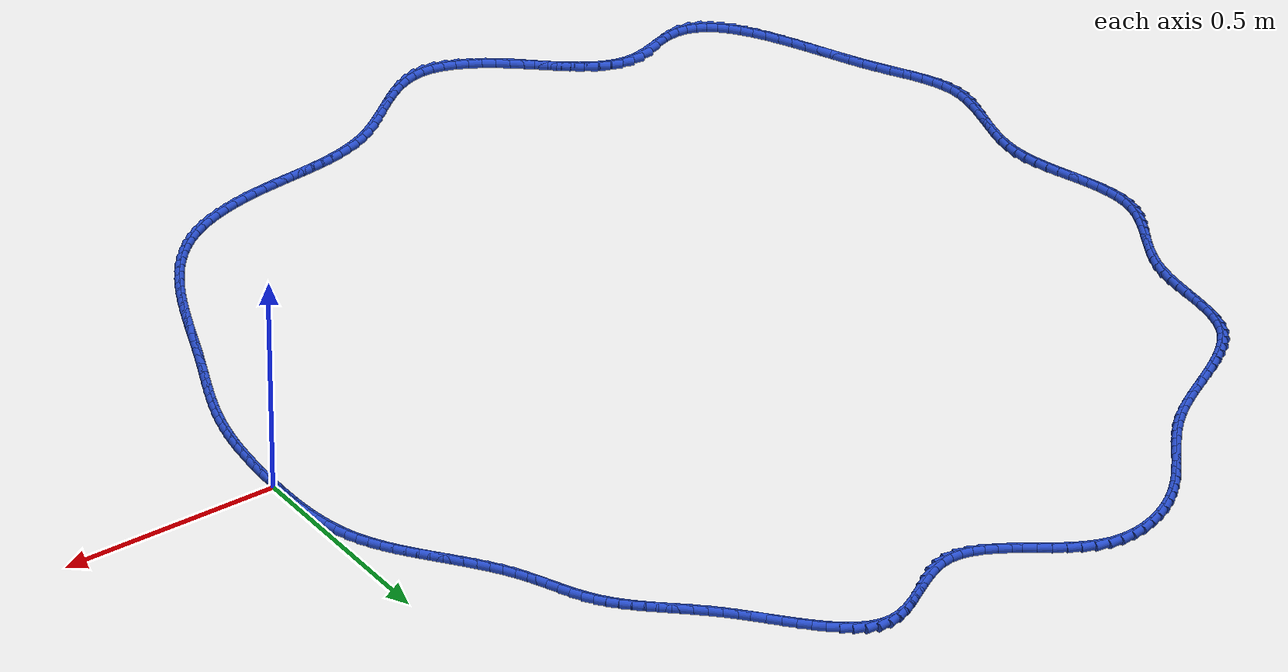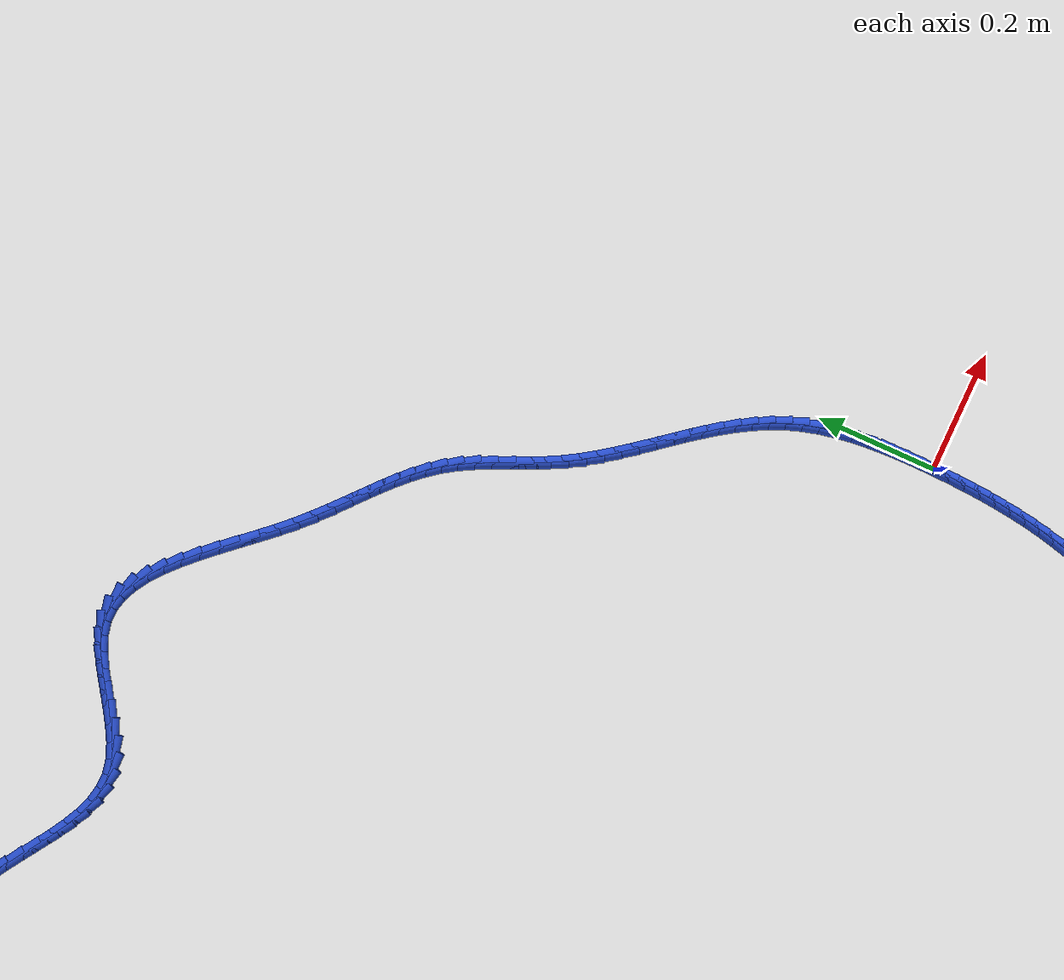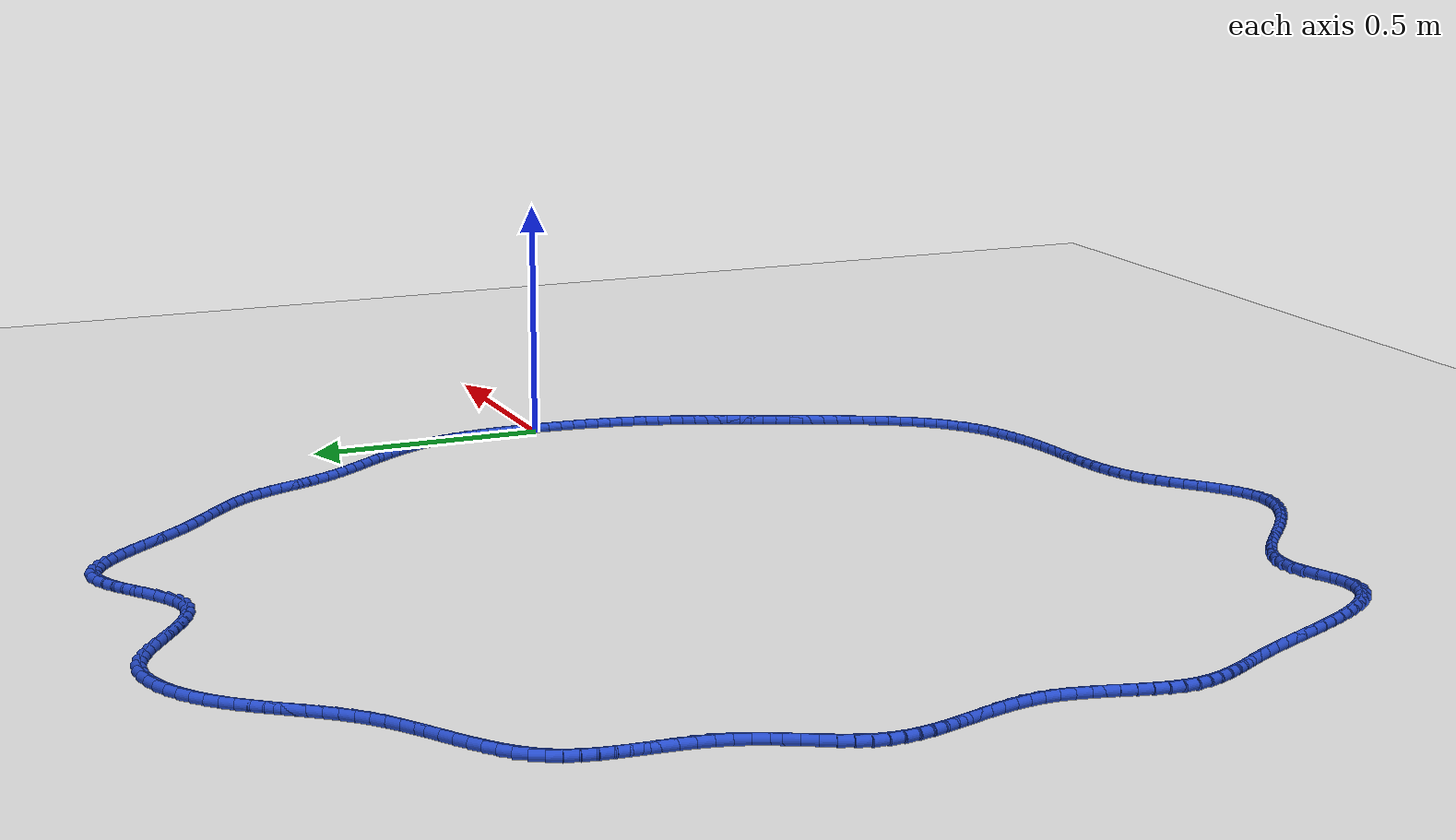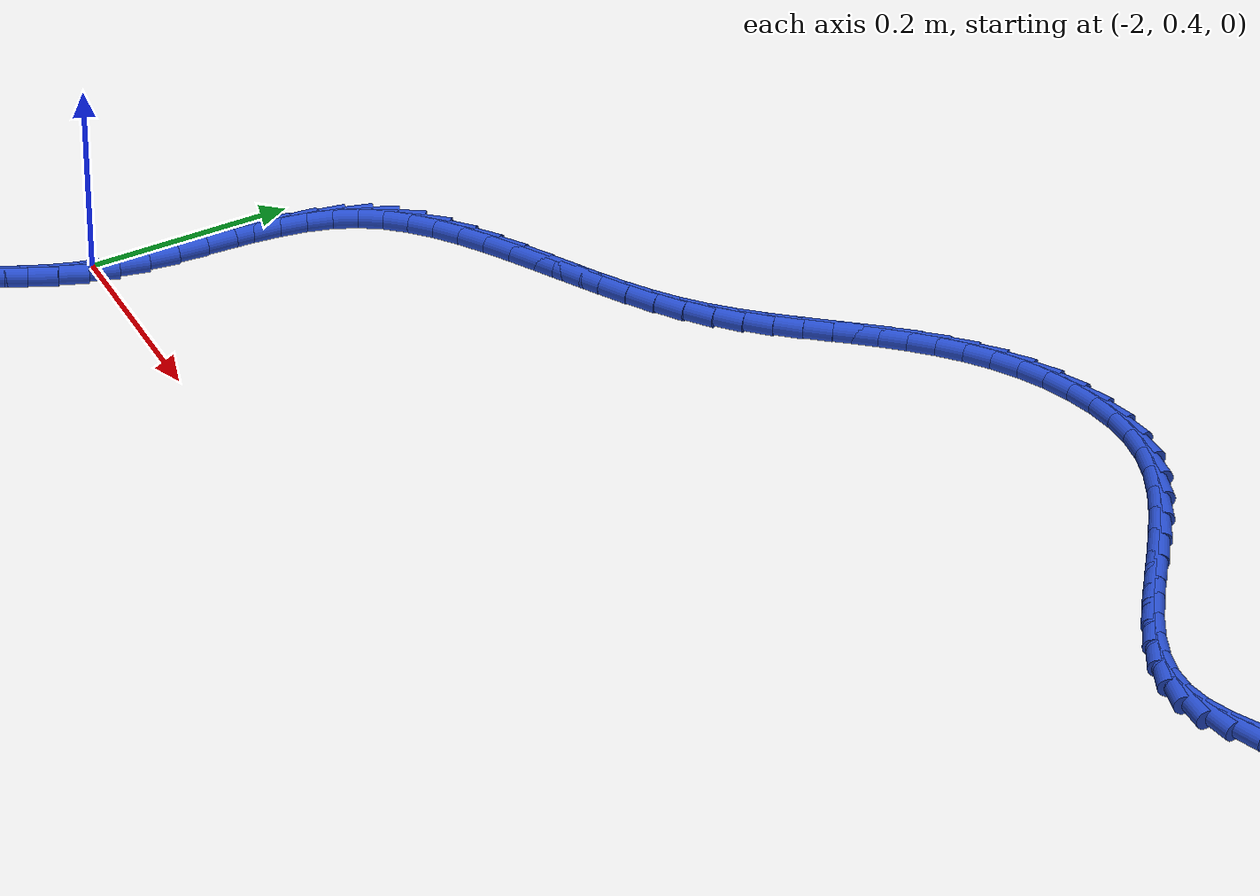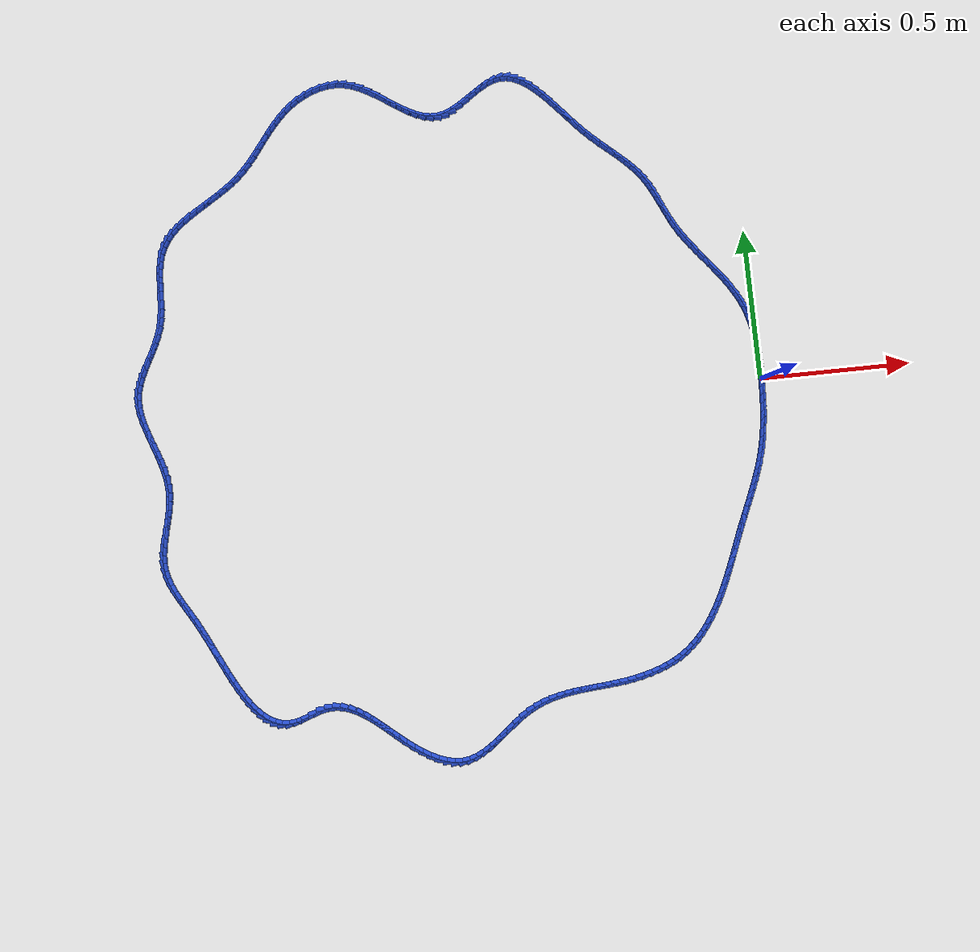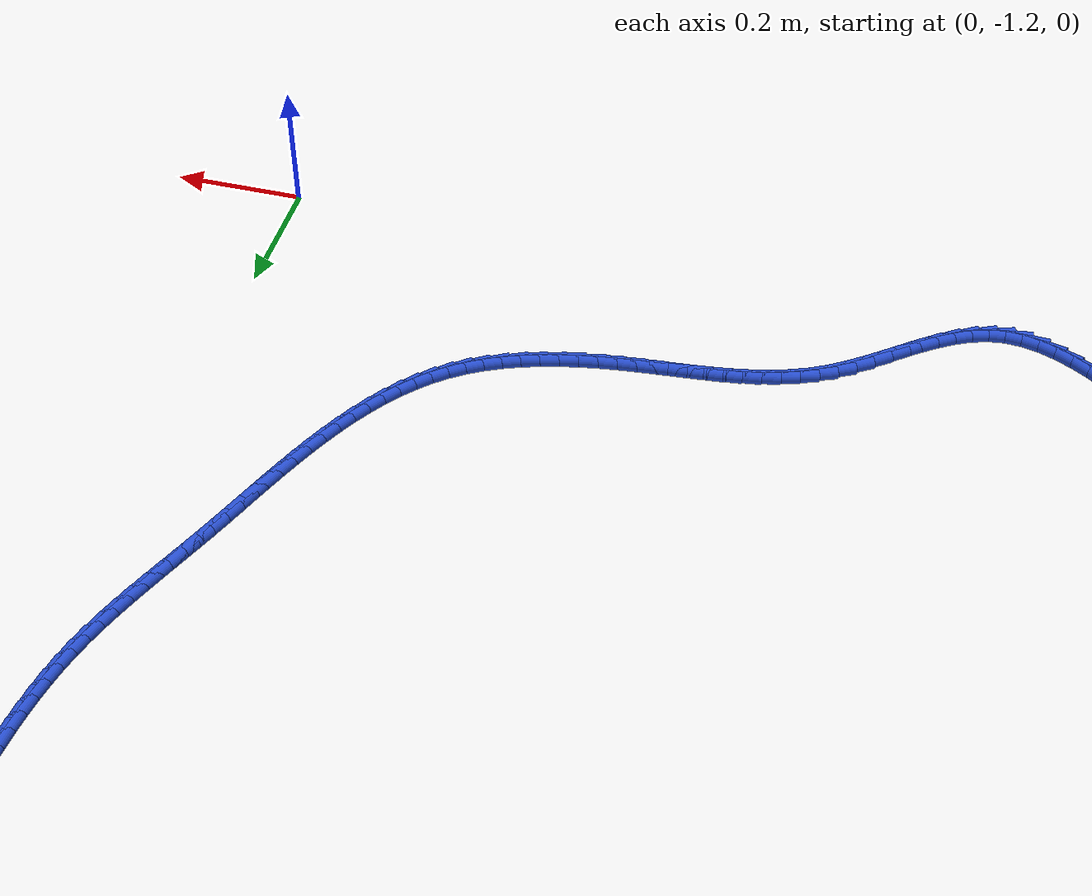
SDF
<sdf version="1.6">
 <world name="default">
  <light name="sun" type="directional">
   <pose>0 0 10 0 -0 0</pose>
   <diffuse>0.8 0.8 0.8 1</diffuse>
   <specular>0.2 0.2 0.2 1</specular>
   <attenuation>
    <range>1000</range>
    <constant>0.9</constant>
    <linear>0.01</linear>
    <quadratic>0.001</quadratic>
   </attenuation>
   <direction>-0.5 0.1 -0.9</direction>
  </light>
  <model name="ground_plane">
   <static>1</static>
   <link name="link">
    <collision name="collision">
     <geometry><plane><normal>0 0 1</normal><size>100 100</size></plane></geometry>
     <surface><friction><ode><mu>100</mu><mu2>50</mu2></ode></friction></surface>
    </collision>
    <visual name="visual">
     <cast_shadows>0</cast_shadows>
     <geometry><plane><normal>0 0 1</normal><size>100 100</size></plane></geometry>
     <material>
      <script><uri>file://media/materials/scripts/gazebo.material</uri><name>Gazebo/WhiteGlow</name></script>
     </material>
    </visual>
   </link>
  </model>
  <gravity>0 0 -9.8</gravity>
  <magnetic_field>6e-06 2.3e-05 -4.2e-05</magnetic_field>
  <atmosphere type="adiabatic"/>
  <physics name="default_physics" default="0" type="ode">
   <max_step_size>0.001</max_step_size>
   <real_time_factor>1</real_time_factor>
   <real_time_update_rate>1000</real_time_update_rate>
  </physics>
  <scene><ambient>0.4 0.4 0.4 1</ambient><background>0.7 0.7 0.7 1</background><shadows>1</shadows></scene>
  <spherical_coordinates>
   <surface_model>EARTH_WGS84</surface_model>
   <latitude_deg>0</latitude_deg>
   <longitude_deg>0</longitude_deg>
   <elevation>0</elevation>
   <heading_deg>0</heading_deg>
  </spherical_coordinates>
  <model name="line">
   <link name="link_0">
    <pose>-1.8323016715005025e-17 -1.3877787807814457e-17 0.01 0 1.57 1.5553200753350904</pose>
    <collision name="collision">
     <geometry><cylinder><radius>0.01</radius><length>0.08</length></cylinder></geometry>
    </collision>
    <visual name="visual">
     <material>
      <script><name>Gazebo/Blue</name><uri>file://media/materials/scripts/gazebo.material</uri></script>
     </material>
     <geometry><cylinder><radius>0.01</radius><length>0.08</length></cylinder></geometry>
    </visual>
   </link>
   <link name="link_1">
    <pose>0.0004414915079881681 0.028524753601993698 0.01 0 1.57 -1.5662697597265813</pose>
    <collision name="collision">
     <geometry><cylinder><radius>0.01</radius><length>0.08</length></cylinder></geometry>
    </collision>
    <visual name="visual">
     <material>
      <script><name>Gazebo/Blue</name><uri>file://media/materials/scripts/gazebo.material</uri></script>
     </material>
     <geometry><cylinder><radius>0.01</radius><length>0.08</length></cylinder></geometry>
    </visual>
   </link>
   <link name="link_2">
    <pose>0.0003122872405282726 0.05706810291104114 0.01 0 1.57 -1.5401163370316076</pose>
    <collision name="collision">
     <geometry><cylinder><radius>0.01</radius><length>0.08</length></cylinder></geometry>
    </collision>
    <visual name="visual">
     <material>
      <script><name>Gazebo/Blue</name><uri>file://media/materials/scripts/gazebo.material</uri></script>
     </material>
     <geometry><cylinder><radius>0.01</radius><length>0.08</length></cylinder></geometry>
    </visual>
   </link>
   <link name="link_3">
    <pose>-0.0005608157806269807 0.08551756039779997 0.01 0 1.57 -1.5074954010092534</pose>
    <collision name="collision">
     <geometry><cylinder><radius>0.01</radius><length>0.08</length></cylinder></geometry>
    </collision>
    <visual name="visual">
     <material>
      <script><name>Gazebo/Blue</name><uri>file://media/materials/scripts/gazebo.material</uri></script>
     </material>
     <geometry><cylinder><radius>0.01</radius><length>0.08</length></cylinder></geometry>
    </visual>
   </link>
   <link name="link_4">
    <pose>-0.0023510205337248648 0.11376063853292764 0.01 0 1.57 -1.4680053422131805</pose>
    <collision name="collision">
     <geometry><cylinder><radius>0.01</radius><length>0.08</length></cylinder></geometry>
    </collision>
    <visual name="visual">
     <material>
      <script><name>Gazebo/Blue</name><uri>file://media/materials/scripts/gazebo.material</uri></script>
     </material>
     <geometry><cylinder><radius>0.01</radius><length>0.08</length></cylinder></geometry>
    </visual>
   </link>
   <link name="link_5">
    <pose>-0.005231529997012659 0.14168484978708182 0.01 0 1.57 -1.4211918492905573</pose>
    <collision name="collision">
     <geometry><cylinder><radius>0.01</radius><length>0.08</length></cylinder></geometry>
    </collision>
    <visual name="visual">
     <material>
      <script><name>Gazebo/Blue</name><uri>file://media/materials/scripts/gazebo.material</uri></script>
     </material>
     <geometry><cylinder><radius>0.01</radius><length>0.08</length></cylinder></geometry>
    </visual>
   </link>
   <link name="link_6">
    <pose>-0.009375547148737635 0.16917770663091997 0.01 0 1.57 -1.3665979591519102</pose>
    <collision name="collision">
     <geometry><cylinder><radius>0.01</radius><length>0.08</length></cylinder></geometry>
    </collision>
    <visual name="visual">
     <material>
      <script><name>Gazebo/Blue</name><uri>file://media/materials/scripts/gazebo.material</uri></script>
     </material>
     <geometry><cylinder><radius>0.01</radius><length>0.08</length></cylinder></geometry>
    </visual>
   </link>
   <link name="link_7">
    <pose>-0.014956274967147068 0.19612672153509964 0.01 0 1.57 -1.3038396258751415</pose>
    <collision name="collision">
     <geometry><cylinder><radius>0.01</radius><length>0.08</length></cylinder></geometry>
    </collision>
    <visual name="visual">
     <material>
      <script><name>Gazebo/Blue</name><uri>file://media/materials/scripts/gazebo.material</uri></script>
     </material>
     <geometry><cylinder><radius>0.01</radius><length>0.08</length></cylinder></geometry>
    </visual>
   </link>
   <link name="link_8">
    <pose>-0.022146916430488234 0.22241940697027843 0.01 0 1.57 -1.2327119643203222</pose>
    <collision name="collision">
     <geometry><cylinder><radius>0.01</radius><length>0.08</length></cylinder></geometry>
    </collision>
    <visual name="visual">
     <material>
      <script><name>Gazebo/Blue</name><uri>file://media/materials/scripts/gazebo.material</uri></script>
     </material>
     <geometry><cylinder><radius>0.01</radius><length>0.08</length></cylinder></geometry>
    </visual>
   </link>
   <link name="link_9">
    <pose>-0.03112067451700842 0.24794327540711397 0.01 0 1.57 -1.1561031268742572</pose>
    <collision name="collision">
     <geometry><cylinder><radius>0.01</radius><length>0.08</length></cylinder></geometry>
    </collision>
    <visual name="visual">
     <material>
      <script><name>Gazebo/Blue</name><uri>file://media/materials/scripts/gazebo.material</uri></script>
     </material>
     <geometry><cylinder><radius>0.01</radius><length>0.08</length></cylinder></geometry>
    </visual>
   </link>
   <link name="link_10">
    <pose>-0.041985241641865775 0.27262299803387424 0.01 0 1.57 -1.0867895096457891</pose>
    <collision name="collision">
     <geometry><cylinder><radius>0.01</radius><length>0.08</length></cylinder></geometry>
    </collision>
    <visual name="visual">
     <material>
      <script><name>Gazebo/Blue</name><uri>file://media/materials/scripts/gazebo.material</uri></script>
     </material>
     <geometry><cylinder><radius>0.01</radius><length>0.08</length></cylinder></geometry>
    </visual>
   </link>
   <link name="link_11">
    <pose>-0.05456178464393703 0.2965457682715059 0.01 0 1.57 -1.0287085036393466</pose>
    <collision name="collision">
     <geometry><cylinder><radius>0.01</radius><length>0.08</length></cylinder></geometry>
    </collision>
    <visual name="visual">
     <material>
      <script><name>Gazebo/Blue</name><uri>file://media/materials/scripts/gazebo.material</uri></script>
     </material>
     <geometry><cylinder><radius>0.01</radius><length>0.08</length></cylinder></geometry>
    </visual>
   </link>
   <link name="link_12">
    <pose>-0.06859315686610178 0.3198432003022136 0.01 0 1.57 -0.9819871982175743</pose>
    <collision name="collision">
     <geometry><cylinder><radius>0.01</radius><length>0.08</length></cylinder></geometry>
    </collision>
    <visual name="visual">
     <material>
      <script><name>Gazebo/Blue</name><uri>file://media/materials/scripts/gazebo.material</uri></script>
     </material>
     <geometry><cylinder><radius>0.01</radius><length>0.08</length></cylinder></geometry>
    </visual>
   </link>
   <link name="link_13">
    <pose>-0.0838222097610074 0.3426469093803737 0.01 0 1.57 -0.9464319955718069</pose>
    <collision name="collision">
     <geometry><cylinder><radius>0.01</radius><length>0.08</length></cylinder></geometry>
    </collision>
    <visual name="visual">
     <material>
      <script><name>Gazebo/Blue</name><uri>file://media/materials/scripts/gazebo.material</uri></script>
     </material>
     <geometry><cylinder><radius>0.01</radius><length>0.08</length></cylinder></geometry>
    </visual>
   </link>
   <link name="link_14">
    <pose>-0.09999179478130135 0.365088510760363 0.01 0 1.57 -0.9217104200919956</pose>
    <collision name="collision">
     <geometry><cylinder><radius>0.01</radius><length>0.08</length></cylinder></geometry>
    </collision>
    <visual name="visual">
     <material>
      <script><name>Gazebo/Blue</name><uri>file://media/materials/scripts/gazebo.material</uri></script>
     </material>
     <geometry><cylinder><radius>0.01</radius><length>0.08</length></cylinder></geometry>
    </visual>
   </link>
   <link name="link_15">
    <pose>-0.11684476337963115 0.3872996196965584 0.01 0 1.57 -0.9074803771943228</pose>
    <collision name="collision">
     <geometry><cylinder><radius>0.01</radius><length>0.08</length></cylinder></geometry>
    </collision>
    <visual name="visual">
     <material>
      <script><name>Gazebo/Blue</name><uri>file://media/materials/scripts/gazebo.material</uri></script>
     </material>
     <geometry><cylinder><radius>0.01</radius><length>0.08</length></cylinder></geometry>
    </visual>
   </link>
   <link name="link_16">
    <pose>-0.13412396700864423 0.4094118514433362 0.01 0 1.57 -0.9034696263075276</pose>
    <collision name="collision">
     <geometry><cylinder><radius>0.01</radius><length>0.08</length></cylinder></geometry>
    </collision>
    <visual name="visual">
     <material>
      <script><name>Gazebo/Blue</name><uri>file://media/materials/scripts/gazebo.material</uri></script>
     </material>
     <geometry><cylinder><radius>0.01</radius><length>0.08</length></cylinder></geometry>
    </visual>
   </link>
   <link name="link_17">
    <pose>-0.15157225712098804 0.4315568212550734 0.01 0 1.57 -0.9095149041295618</pose>
    <collision name="collision">
     <geometry><cylinder><radius>0.01</radius><length>0.08</length></cylinder></geometry>
    </collision>
    <visual name="visual">
     <material>
      <script><name>Gazebo/Blue</name><uri>file://media/materials/scripts/gazebo.material</uri></script>
     </material>
     <geometry><cylinder><radius>0.01</radius><length>0.08</length></cylinder></geometry>
    </visual>
   </link>
   <link name="link_18">
    <pose>-0.1689324851693101 0.45386614438614653 0.01 0 1.57 -0.9255690504939411</pose>
    <collision name="collision">
     <geometry><cylinder><radius>0.01</radius><length>0.08</length></cylinder></geometry>
    </collision>
    <visual name="visual">
     <material>
      <script><name>Gazebo/Blue</name><uri>file://media/materials/scripts/gazebo.material</uri></script>
     </material>
     <geometry><cylinder><radius>0.01</radius><length>0.08</length></cylinder></geometry>
    </visual>
   </link>
   <link name="link_19">
    <pose>-0.1859475026062577 0.47647143609093207 0.01 0 1.57 -0.9516803264550063</pose>
    <collision name="collision">
     <geometry><cylinder><radius>0.01</radius><length>0.08</length></cylinder></geometry>
    </collision>
    <visual name="visual">
     <material>
      <script><name>Gazebo/Blue</name><uri>file://media/materials/scripts/gazebo.material</uri></script>
     </material>
     <geometry><cylinder><radius>0.01</radius><length>0.08</length></cylinder></geometry>
    </visual>
   </link>
   <link name="link_20">
    <pose>-0.20236016088447845 0.49950431162380693 0.01 0 1.57 -0.9879437023587974</pose>
    <collision name="collision">
     <geometry><cylinder><radius>0.01</radius><length>0.08</length></cylinder></geometry>
    </collision>
    <visual name="visual">
     <material>
      <script><name>Gazebo/Blue</name><uri>file://media/materials/scripts/gazebo.material</uri></script>
     </material>
     <geometry><cylinder><radius>0.01</radius><length>0.08</length></cylinder></geometry>
    </visual>
   </link>
   <link name="link_21">
    <pose>-0.21791331145661982 0.5230963862391478 0.01 0 1.57 -1.0344211183286065</pose>
    <collision name="collision">
     <geometry><cylinder><radius>0.01</radius><length>0.08</length></cylinder></geometry>
    </collision>
    <visual name="visual">
     <material>
      <script><name>Gazebo/Blue</name><uri>file://media/materials/scripts/gazebo.material</uri></script>
     </material>
     <geometry><cylinder><radius>0.01</radius><length>0.08</length></cylinder></geometry>
    </visual>
   </link>
   <link name="link_22">
    <pose>-0.23234980577532913 0.5473792751913311 0.01 0 1.57 -1.0879802597897867</pose>
    <collision name="collision">
     <geometry><cylinder><radius>0.01</radius><length>0.08</length></cylinder></geometry>
    </collision>
    <visual name="visual">
     <material>
      <script><name>Gazebo/Blue</name><uri>file://media/materials/scripts/gazebo.material</uri></script>
     </material>
     <geometry><cylinder><radius>0.01</radius><length>0.08</length></cylinder></geometry>
    </visual>
   </link>
   <link name="link_23">
    <pose>-0.24548372207166536 0.5724346563186403 0.01 0 1.57 -1.1280250603066968</pose>
    <collision name="collision">
     <geometry><cylinder><radius>0.01</radius><length>0.08</length></cylinder></geometry>
    </collision>
    <visual name="visual">
     <material>
      <script><name>Gazebo/Blue</name><uri>file://media/materials/scripts/gazebo.material</uri></script>
     </material>
     <geometry><cylinder><radius>0.01</radius><length>0.08</length></cylinder></geometry>
    </visual>
   </link>
   <link name="link_24">
    <pose>-0.25760955429303556 0.5980073858304675 0.01 0 1.57 -1.1463990120088077</pose>
    <collision name="collision">
     <geometry><cylinder><radius>0.01</radius><length>0.08</length></cylinder></geometry>
    </collision>
    <visual name="visual">
     <material>
      <script><name>Gazebo/Blue</name><uri>file://media/materials/scripts/gazebo.material</uri></script>
     </material>
     <geometry><cylinder><radius>0.01</radius><length>0.08</length></cylinder></geometry>
    </visual>
   </link>
   <link name="link_25">
    <pose>-0.26922035310306563 0.6237031109255334 0.01 0 1.57 -1.1430899124916272</pose>
    <collision name="collision">
     <geometry><cylinder><radius>0.01</radius><length>0.08</length></cylinder></geometry>
    </collision>
    <visual name="visual">
     <material>
      <script><name>Gazebo/Blue</name><uri>file://media/materials/scripts/gazebo.material</uri></script>
     </material>
     <geometry><cylinder><radius>0.01</radius><length>0.08</length></cylinder></geometry>
    </visual>
   </link>
   <link name="link_26">
    <pose>-0.2808097977449292 0.6491270381025981 0.01 0 1.57 -1.1174411921694796</pose>
    <collision name="collision">
     <geometry><cylinder><radius>0.01</radius><length>0.08</length></cylinder></geometry>
    </collision>
    <visual name="visual">
     <material>
      <script><name>Gazebo/Blue</name><uri>file://media/materials/scripts/gazebo.material</uri></script>
     </material>
     <geometry><cylinder><radius>0.01</radius><length>0.08</length></cylinder></geometry>
    </visual>
   </link>
   <link name="link_27">
    <pose>-0.29287156746179993 0.6738843738604215 0.01 0 1.57 -1.0681150966436035</pose>
    <collision name="collision">
     <geometry><cylinder><radius>0.01</radius><length>0.08</length></cylinder></geometry>
    </collision>
    <visual name="visual">
     <material>
      <script><name>Gazebo/Blue</name><uri>file://media/materials/scripts/gazebo.material</uri></script>
     </material>
     <geometry><cylinder><radius>0.01</radius><length>0.08</length></cylinder></geometry>
    </visual>
   </link>
   <link name="link_28">
    <pose>-0.3058993414968514 0.6975803246977645 0.01 0 1.57 -0.9942347466215452</pose>
    <collision name="collision">
     <geometry><cylinder><radius>0.01</radius><length>0.08</length></cylinder></geometry>
    </collision>
    <visual name="visual">
     <material>
      <script><name>Gazebo/Blue</name><uri>file://media/materials/scripts/gazebo.material</uri></script>
     </material>
     <geometry><cylinder><radius>0.01</radius><length>0.08</length></cylinder></geometry>
    </visual>
   </link>
   <link name="link_29">
    <pose>-0.32037165580176774 0.7198363456157624 0.01 0 1.57 -0.9131866756456802</pose>
    <collision name="collision">
     <geometry><cylinder><radius>0.01</radius><length>0.08</length></cylinder></geometry>
    </collision>
    <visual name="visual">
     <material>
      <script><name>Gazebo/Blue</name><uri>file://media/materials/scripts/gazebo.material</uri></script>
     </material>
     <geometry><cylinder><radius>0.01</radius><length>0.08</length></cylinder></geometry>
    </visual>
   </link>
   <link name="link_30">
    <pose>-0.33643245734391874 0.7406329000854154 0.01 0 1.57 -0.8446395364521905</pose>
    <collision name="collision">
     <geometry><cylinder><radius>0.01</radius><length>0.08</length></cylinder></geometry>
    </collision>
    <visual name="visual">
     <material>
      <script><name>Gazebo/Blue</name><uri>file://media/materials/scripts/gazebo.material</uri></script>
     </material>
     <geometry><cylinder><radius>0.01</radius><length>0.08</length></cylinder></geometry>
    </visual>
   </link>
   <link name="link_31">
    <pose>-0.3538985463113718 0.7603014746841779 0.01 0 1.57 -0.7910478218169394</pose>
    <collision name="collision">
     <geometry><cylinder><radius>0.01</radius><length>0.08</length></cylinder></geometry>
    </collision>
    <visual name="visual">
     <material>
      <script><name>Gazebo/Blue</name><uri>file://media/materials/scripts/gazebo.material</uri></script>
     </material>
     <geometry><cylinder><radius>0.01</radius><length>0.08</length></cylinder></geometry>
    </visual>
   </link>
   <link name="link_32">
    <pose>-0.3725730682777986 0.7791882071658727 0.01 0 1.57 -0.7530244384197256</pose>
    <collision name="collision">
     <geometry><cylinder><radius>0.01</radius><length>0.08</length></cylinder></geometry>
    </collision>
    <visual name="visual">
     <material>
      <script><name>Gazebo/Blue</name><uri>file://media/materials/scripts/gazebo.material</uri></script>
     </material>
     <geometry><cylinder><radius>0.01</radius><length>0.08</length></cylinder></geometry>
    </visual>
   </link>
   <link name="link_33">
    <pose>-0.39225916881687106 0.7976392352843239 0.01 0 1.57 -0.7304038179022013</pose>
    <collision name="collision">
     <geometry><cylinder><radius>0.01</radius><length>0.08</length></cylinder></geometry>
    </collision>
    <visual name="visual">
     <material>
      <script><name>Gazebo/Blue</name><uri>file://media/materials/scripts/gazebo.material</uri></script>
     </material>
     <geometry><cylinder><radius>0.01</radius><length>0.08</length></cylinder></geometry>
    </visual>
   </link>
   <link name="link_34">
    <pose>-0.4127599935022609 0.8160006967933551 0.01 0 1.57 -0.7225502981332543</pose>
    <collision name="collision">
     <geometry><cylinder><radius>0.01</radius><length>0.08</length></cylinder></geometry>
    </collision>
    <visual name="visual">
     <material>
      <script><name>Gazebo/Blue</name><uri>file://media/materials/scripts/gazebo.material</uri></script>
     </material>
     <geometry><cylinder><radius>0.01</radius><length>0.08</length></cylinder></geometry>
    </visual>
   </link>
   <link name="link_35">
    <pose>-0.43387868790764006 0.8346187294467898 0.01 0 1.57 -0.7285668247678208</pose>
    <collision name="collision">
     <geometry><cylinder><radius>0.01</radius><length>0.08</length></cylinder></geometry>
    </collision>
    <visual name="visual">
     <material>
      <script><name>Gazebo/Blue</name><uri>file://media/materials/scripts/gazebo.material</uri></script>
     </material>
     <geometry><cylinder><radius>0.01</radius><length>0.08</length></cylinder></geometry>
    </visual>
   </link>
   <link name="link_36">
    <pose>-0.45541839760668024 0.8538394709984516 0.01 0 1.57 -0.7473971276510487</pose>
    <collision name="collision">
     <geometry><cylinder><radius>0.01</radius><length>0.08</length></cylinder></geometry>
    </collision>
    <visual name="visual">
     <material>
      <script><name>Gazebo/Blue</name><uri>file://media/materials/scripts/gazebo.material</uri></script>
     </material>
     <geometry><cylinder><radius>0.01</radius><length>0.08</length></cylinder></geometry>
    </visual>
   </link>
   <link name="link_37">
    <pose>-0.4771822681730533 0.8740090592021643 0.01 0 1.57 -0.7778477638726008</pose>
    <collision name="collision">
     <geometry><cylinder><radius>0.01</radius><length>0.08</length></cylinder></geometry>
    </collision>
    <visual name="visual">
     <material>
      <script><name>Gazebo/Blue</name><uri>file://media/materials/scripts/gazebo.material</uri></script>
     </material>
     <geometry><cylinder><radius>0.01</radius><length>0.08</length></cylinder></geometry>
    </visual>
   </link>
   <link name="link_38">
    <pose>-0.4989734451804314 0.8954736318117514 0.01 0 1.57 -0.8150539953276795</pose>
    <collision name="collision">
     <geometry><cylinder><radius>0.01</radius><length>0.08</length></cylinder></geometry>
    </collision>
    <visual name="visual">
     <material>
      <script><name>Gazebo/Blue</name><uri>file://media/materials/scripts/gazebo.material</uri></script>
     </material>
     <geometry><cylinder><radius>0.01</radius><length>0.08</length></cylinder></geometry>
    </visual>
   </link>
   <link name="link_39">
    <pose>-0.5206281834407767 0.9184524020700275 0.01 0 1.57 -0.8412696189431139</pose>
    <collision name="collision">
     <geometry><cylinder><radius>0.01</radius><length>0.08</length></cylinder></geometry>
    </collision>
    <visual name="visual">
     <material>
      <script><name>Gazebo/Blue</name><uri>file://media/materials/scripts/gazebo.material</uri></script>
     </material>
     <geometry><cylinder><radius>0.01</radius><length>0.08</length></cylinder></geometry>
    </visual>
   </link>
   <link name="link_40">
    <pose>-0.542149823261442 0.9425240597316914 0.01 0 1.57 -0.8526468074825505</pose>
    <collision name="collision">
     <geometry><cylinder><radius>0.01</radius><length>0.08</length></cylinder></geometry>
    </collision>
    <visual name="visual">
     <material>
      <script><name>Gazebo/Blue</name><uri>file://media/materials/scripts/gazebo.material</uri></script>
     </material>
     <geometry><cylinder><radius>0.01</radius><length>0.08</length></cylinder></geometry>
    </visual>
   </link>
   <link name="link_41">
    <pose>-0.5635942918637209 0.9670657022260921 0.01 0 1.57 -0.8500380391556757</pose>
    <collision name="collision">
     <geometry><cylinder><radius>0.01</radius><length>0.08</length></cylinder></geometry>
    </collision>
    <visual name="visual">
     <material>
      <script><name>Gazebo/Blue</name><uri>file://media/materials/scripts/gazebo.material</uri></script>
     </material>
     <geometry><cylinder><radius>0.01</radius><length>0.08</length></cylinder></geometry>
    </visual>
   </link>
   <link name="link_42">
    <pose>-0.5850175358551398 0.9914543526653163 0.01 0 1.57 -0.8331693027049593</pose>
    <collision name="collision">
     <geometry><cylinder><radius>0.01</radius><length>0.08</length></cylinder></geometry>
    </collision>
    <visual name="visual">
     <material>
      <script><name>Gazebo/Blue</name><uri>file://media/materials/scripts/gazebo.material</uri></script>
     </material>
     <geometry><cylinder><radius>0.01</radius><length>0.08</length></cylinder></geometry>
    </visual>
   </link>
   <link name="link_43">
    <pose>-0.6064755018432245 1.0150670341614507 0.01 0 1.57 -0.8005950064335479</pose>
    <collision name="collision">
     <geometry><cylinder><radius>0.01</radius><length>0.08</length></cylinder></geometry>
    </collision>
    <visual name="visual">
     <material>
      <script><name>Gazebo/Blue</name><uri>file://media/materials/scripts/gazebo.material</uri></script>
     </material>
     <geometry><cylinder><radius>0.01</radius><length>0.08</length></cylinder></geometry>
    </visual>
   </link>
   <link name="link_44">
    <pose>-0.628024136435501 1.037280769826581 0.01 0 1.57 -0.7495209344546828</pose>
    <collision name="collision">
     <geometry><cylinder><radius>0.01</radius><length>0.08</length></cylinder></geometry>
    </collision>
    <visual name="visual">
     <material>
      <script><name>Gazebo/Blue</name><uri>file://media/materials/scripts/gazebo.material</uri></script>
     </material>
     <geometry><cylinder><radius>0.01</radius><length>0.08</length></cylinder></geometry>
    </visual>
   </link>
   <link name="link_45">
    <pose>-0.6497193862394959 1.0574725827727944 0.01 0 1.57 -0.6755385980376114</pose>
    <collision name="collision">
     <geometry><cylinder><radius>0.01</radius><length>0.08</length></cylinder></geometry>
    </collision>
    <visual name="visual">
     <material>
      <script><name>Gazebo/Blue</name><uri>file://media/materials/scripts/gazebo.material</uri></script>
     </material>
     <geometry><cylinder><radius>0.01</radius><length>0.08</length></cylinder></geometry>
    </visual>
   </link>
   <link name="link_46">
    <pose>-0.6716171978627345 1.0750194961121762 0.01 0 1.57 -0.572476379702755</pose>
    <collision name="collision">
     <geometry><cylinder><radius>0.01</radius><length>0.08</length></cylinder></geometry>
    </collision>
    <visual name="visual">
     <material>
      <script><name>Gazebo/Blue</name><uri>file://media/materials/scripts/gazebo.material</uri></script>
     </material>
     <geometry><cylinder><radius>0.01</radius><length>0.08</length></cylinder></geometry>
    </visual>
   </link>
   <link name="link_47">
    <pose>-0.6937735179127431 1.0892985329568132 0.01 0 1.57 -0.4330333503650212</pose>
    <collision name="collision">
     <geometry><cylinder><radius>0.01</radius><length>0.08</length></cylinder></geometry>
    </collision>
    <visual name="visual">
     <material>
      <script><name>Gazebo/Blue</name><uri>file://media/materials/scripts/gazebo.material</uri></script>
     </material>
     <geometry><cylinder><radius>0.01</radius><length>0.08</length></cylinder></geometry>
    </visual>
   </link>
   <link name="link_48">
    <pose>-0.7162442929970478 1.0996867164187922 0.01 0 1.57 -0.2517272482778761</pose>
    <collision name="collision">
     <geometry><cylinder><radius>0.01</radius><length>0.08</length></cylinder></geometry>
    </collision>
    <visual name="visual">
     <material>
      <script><name>Gazebo/Blue</name><uri>file://media/materials/scripts/gazebo.material</uri></script>
     </material>
     <geometry><cylinder><radius>0.01</radius><length>0.08</length></cylinder></geometry>
    </visual>
   </link>
   <link name="link_49">
    <pose>-0.7390854697231748 1.1055610696101987 0.01 0 1.57 -0.031687906417101355</pose>
    <collision name="collision">
     <geometry><cylinder><radius>0.01</radius><length>0.08</length></cylinder></geometry>
    </collision>
    <visual name="visual">
     <material>
      <script><name>Gazebo/Blue</name><uri>file://media/materials/scripts/gazebo.material</uri></script>
     </material>
     <geometry><cylinder><radius>0.01</radius><length>0.08</length></cylinder></geometry>
    </visual>
   </link>
   <link name="link_50">
    <pose>-0.7623529946986495 1.1062986156431194 0.01 0 1.57 0.20481816619805995</pose>
    <collision name="collision">
     <geometry><cylinder><radius>0.01</radius><length>0.08</length></cylinder></geometry>
    </collision>
    <visual name="visual">
     <material>
      <script><name>Gazebo/Blue</name><uri>file://media/materials/scripts/gazebo.material</uri></script>
     </material>
     <geometry><cylinder><radius>0.01</radius><length>0.08</length></cylinder></geometry>
    </visual>
   </link>
   <link name="link_51">
    <pose>-0.7860967618240448 1.1013662960769313 0.01 0 1.57 0.39125382967165334</pose>
    <collision name="collision">
     <geometry><cylinder><radius>0.01</radius><length>0.08</length></cylinder></geometry>
    </collision>
    <visual name="visual">
     <material>
      <script><name>Gazebo/Blue</name><uri>file://media/materials/scripts/gazebo.material</uri></script>
     </material>
     <geometry><cylinder><radius>0.01</radius><length>0.08</length></cylinder></geometry>
    </visual>
   </link>
   <link name="link_52">
    <pose>-0.8102888861247144 1.0913865281522825 0.01 0 1.57 0.5058451874363917</pose>
    <collision name="collision">
     <geometry><cylinder><radius>0.01</radius><length>0.08</length></cylinder></geometry>
    </collision>
    <visual name="visual">
     <material>
      <script><name>Gazebo/Blue</name><uri>file://media/materials/scripts/gazebo.material</uri></script>
     </material>
     <geometry><cylinder><radius>0.01</radius><length>0.08</length></cylinder></geometry>
    </visual>
   </link>
   <link name="link_53">
    <pose>-0.8348475408704312 1.0777830827756736 0.01 0 1.57 0.5661136860215664</pose>
    <collision name="collision">
     <geometry><cylinder><radius>0.01</radius><length>0.08</length></cylinder></geometry>
    </collision>
    <visual name="visual">
     <material>
      <script><name>Gazebo/Blue</name><uri>file://media/materials/scripts/gazebo.material</uri></script>
     </material>
     <geometry><cylinder><radius>0.01</radius><length>0.08</length></cylinder></geometry>
    </visual>
   </link>
   <link name="link_54">
    <pose>-0.8596898151124833 1.0619958379018049 0.01 0 1.57 0.5834508233717084</pose>
    <collision name="collision">
     <geometry><cylinder><radius>0.01</radius><length>0.08</length></cylinder></geometry>
    </collision>
    <visual name="visual">
     <material>
      <script><name>Gazebo/Blue</name><uri>file://media/materials/scripts/gazebo.material</uri></script>
     </material>
     <geometry><cylinder><radius>0.01</radius><length>0.08</length></cylinder></geometry>
    </visual>
   </link>
   <link name="link_55">
    <pose>-0.8847327979021584 1.0454646714853775 0.01 0 1.57 0.5617290595081829</pose>
    <collision name="collision">
     <geometry><cylinder><radius>0.01</radius><length>0.08</length></cylinder></geometry>
    </collision>
    <visual name="visual">
     <material>
      <script><name>Gazebo/Blue</name><uri>file://media/materials/scripts/gazebo.material</uri></script>
     </material>
     <geometry><cylinder><radius>0.01</radius><length>0.08</length></cylinder></geometry>
    </visual>
   </link>
   <link name="link_56">
    <pose>-0.909893578290744 1.0296294614810921 0.01 0 1.57 0.49800855048501697</pose>
    <collision name="collision">
     <geometry><cylinder><radius>0.01</radius><length>0.08</length></cylinder></geometry>
    </collision>
    <visual name="visual">
     <material>
      <script><name>Gazebo/Blue</name><uri>file://media/materials/scripts/gazebo.material</uri></script>
     </material>
     <geometry><cylinder><radius>0.01</radius><length>0.08</length></cylinder></geometry>
    </visual>
   </link>
   <link name="link_57">
    <pose>-0.9350892453295286 1.0159300858436504 0.01 0 1.57 0.3827191344237403</pose>
    <collision name="collision">
     <geometry><cylinder><radius>0.01</radius><length>0.08</length></cylinder></geometry>
    </collision>
    <visual name="visual">
     <material>
      <script><name>Gazebo/Blue</name><uri>file://media/materials/scripts/gazebo.material</uri></script>
     </material>
     <geometry><cylinder><radius>0.01</radius><length>0.08</length></cylinder></geometry>
    </visual>
   </link>
   <link name="link_58">
    <pose>-0.9602368880697992 1.005806422527753 0.01 0 1.57 0.20195522690429837</pose>
    <collision name="collision">
     <geometry><cylinder><radius>0.01</radius><length>0.08</length></cylinder></geometry>
    </collision>
    <visual name="visual">
     <material>
      <script><name>Gazebo/Blue</name><uri>file://media/materials/scripts/gazebo.material</uri></script>
     </material>
     <geometry><cylinder><radius>0.01</radius><length>0.08</length></cylinder></geometry>
    </visual>
   </link>
   <link name="link_59">
    <pose>-0.985254494884375 1.000684157219472 0.01 0 1.57 -0.018389282301375227</pose>
    <collision name="collision">
     <geometry><cylinder><radius>0.01</radius><length>0.08</length></cylinder></geometry>
    </collision>
    <visual name="visual">
     <material>
      <script><name>Gazebo/Blue</name><uri>file://media/materials/scripts/gazebo.material</uri></script>
     </material>
     <geometry><cylinder><radius>0.01</radius><length>0.08</length></cylinder></geometry>
    </visual>
   </link>
   <link name="link_60">
    <pose>-1.0101137654566448 1.00114135290096 0.01 0 1.57 -0.21102950709271842</pose>
    <collision name="collision">
     <geometry><cylinder><radius>0.01</radius><length>0.08</length></cylinder></geometry>
    </collision>
    <visual name="visual">
     <material>
      <script><name>Gazebo/Blue</name><uri>file://media/materials/scripts/gazebo.material</uri></script>
     </material>
     <geometry><cylinder><radius>0.01</radius><length>0.08</length></cylinder></geometry>
    </visual>
   </link>
   <link name="link_61">
    <pose>-1.0348695097243301 1.0064445026493538 0.01 0 1.57 -0.3600196760487793</pose>
    <collision name="collision">
     <geometry><cylinder><radius>0.01</radius><length>0.08</length></cylinder></geometry>
    </collision>
    <visual name="visual">
     <material>
      <script><name>Gazebo/Blue</name><uri>file://media/materials/scripts/gazebo.material</uri></script>
     </material>
     <geometry><cylinder><radius>0.01</radius><length>0.08</length></cylinder></geometry>
    </visual>
   </link>
   <link name="link_62">
    <pose>-1.0595836702912398 1.0157475383391132 0.01 0 1.57 -0.46654118120550203</pose>
    <collision name="collision">
     <geometry><cylinder><radius>0.01</radius><length>0.08</length></cylinder></geometry>
    </collision>
    <visual name="visual">
     <material>
      <script><name>Gazebo/Blue</name><uri>file://media/materials/scripts/gazebo.material</uri></script>
     </material>
     <geometry><cylinder><radius>0.01</radius><length>0.08</length></cylinder></geometry>
    </visual>
   </link>
   <link name="link_63">
    <pose>-1.084318189761183 1.0282043918446997 0.01 0 1.57 -0.5366930967888984</pose>
    <collision name="collision">
     <geometry><cylinder><radius>0.01</radius><length>0.08</length></cylinder></geometry>
    </collision>
    <visual name="visual">
     <material>
      <script><name>Gazebo/Blue</name><uri>file://media/materials/scripts/gazebo.material</uri></script>
     </material>
     <geometry><cylinder><radius>0.01</radius><length>0.08</length></cylinder></geometry>
    </visual>
   </link>
   <link name="link_64">
    <pose>-1.1091350107379692 1.0429689950405736 0.01 0 1.57 -0.5764200681480977</pose>
    <collision name="collision">
     <geometry><cylinder><radius>0.01</radius><length>0.08</length></cylinder></geometry>
    </collision>
    <visual name="visual">
     <material>
      <script><name>Gazebo/Blue</name><uri>file://media/materials/scripts/gazebo.material</uri></script>
     </material>
     <geometry><cylinder><radius>0.01</radius><length>0.08</length></cylinder></geometry>
    </visual>
   </link>
   <link name="link_65">
    <pose>-1.1340960758254066 1.0591952798011952 0.01 0 1.57 -0.5897536667342413</pose>
    <collision name="collision">
     <geometry><cylinder><radius>0.01</radius><length>0.08</length></cylinder></geometry>
    </collision>
    <visual name="visual">
     <material>
      <script><name>Gazebo/Blue</name><uri>file://media/materials/scripts/gazebo.material</uri></script>
     </material>
     <geometry><cylinder><radius>0.01</radius><length>0.08</length></cylinder></geometry>
    </visual>
   </link>
   <link name="link_66">
    <pose>-1.1592633276273043 1.0760371780010252 0.01 0 1.57 -0.5785402649932369</pose>
    <collision name="collision">
     <geometry><cylinder><radius>0.01</radius><length>0.08</length></cylinder></geometry>
    </collision>
    <visual name="visual">
     <material>
      <script><name>Gazebo/Blue</name><uri>file://media/materials/scripts/gazebo.material</uri></script>
     </material>
     <geometry><cylinder><radius>0.01</radius><length>0.08</length></cylinder></geometry>
    </visual>
   </link>
   <link name="link_67">
    <pose>-1.1846987087474719 1.0926486215145246 0.01 0 1.57 -0.54257557063632</pose>
    <collision name="collision">
     <geometry><cylinder><radius>0.01</radius><length>0.08</length></cylinder></geometry>
    </collision>
    <visual name="visual">
     <material>
      <script><name>Gazebo/Blue</name><uri>file://media/materials/scripts/gazebo.material</uri></script>
     </material>
     <geometry><cylinder><radius>0.01</radius><length>0.08</length></cylinder></geometry>
    </visual>
   </link>
   <link name="link_68">
    <pose>-1.210464161789718 1.1081835422161532 0.01 0 1.57 -0.47983360979448114</pose>
    <collision name="collision">
     <geometry><cylinder><radius>0.01</radius><length>0.08</length></cylinder></geometry>
    </collision>
    <visual name="visual">
     <material>
      <script><name>Gazebo/Blue</name><uri>file://media/materials/scripts/gazebo.material</uri></script>
     </material>
     <geometry><cylinder><radius>0.01</radius><length>0.08</length></cylinder></geometry>
    </visual>
   </link>
   <link name="link_69">
    <pose>-1.236621629357852 1.1217958719803722 0.01 0 1.57 -0.38693950141402556</pose>
    <collision name="collision">
     <geometry><cylinder><radius>0.01</radius><length>0.08</length></cylinder></geometry>
    </collision>
    <visual name="visual">
     <material>
      <script><name>Gazebo/Blue</name><uri>file://media/materials/scripts/gazebo.material</uri></script>
     </material>
     <geometry><cylinder><radius>0.01</radius><length>0.08</length></cylinder></geometry>
    </visual>
   </link>
   <link name="link_70">
    <pose>-1.2632330540556822 1.132639542681642 0.01 0 1.57 -0.2604299718025255</pose>
    <collision name="collision">
     <geometry><cylinder><radius>0.01</radius><length>0.08</length></cylinder></geometry>
    </collision>
    <visual name="visual">
     <material>
      <script><name>Gazebo/Blue</name><uri>file://media/materials/scripts/gazebo.material</uri></script>
     </material>
     <geometry><cylinder><radius>0.01</radius><length>0.08</length></cylinder></geometry>
    </visual>
   </link>
   <link name="link_71">
    <pose>-1.2903603784870183 1.1398684861944228 0.01 0 1.57 -0.1039151474428411</pose>
    <collision name="collision">
     <geometry><cylinder><radius>0.01</radius><length>0.08</length></cylinder></geometry>
    </collision>
    <visual name="visual">
     <material>
      <script><name>Gazebo/Blue</name><uri>file://media/materials/scripts/gazebo.material</uri></script>
     </material>
     <geometry><cylinder><radius>0.01</radius><length>0.08</length></cylinder></geometry>
    </visual>
   </link>
   <link name="link_72">
    <pose>-1.3180251527663653 1.142753667851129 0.01 0 1.57 0.04909680339785257</pose>
    <collision name="collision">
     <geometry><cylinder><radius>0.01</radius><length>0.08</length></cylinder></geometry>
    </collision>
    <visual name="visual">
     <material>
      <script><name>Gazebo/Blue</name><uri>file://media/materials/scripts/gazebo.material</uri></script>
     </material>
     <geometry><cylinder><radius>0.01</radius><length>0.08</length></cylinder></geometry>
    </visual>
   </link>
   <link name="link_73">
    <pose>-1.3459677727446917 1.1413806711532437 0.01 0 1.57 0.18462029657132842</pose>
    <collision name="collision">
     <geometry><cylinder><radius>0.01</radius><length>0.08</length></cylinder></geometry>
    </collision>
    <visual name="visual">
     <material>
      <script><name>Gazebo/Blue</name><uri>file://media/materials/scripts/gazebo.material</uri></script>
     </material>
     <geometry><cylinder><radius>0.01</radius><length>0.08</length></cylinder></geometry>
    </visual>
   </link>
   <link name="link_74">
    <pose>-1.373809110504782 1.1361813885359002 0.01 0 1.57 0.3042912069913193</pose>
    <collision name="collision">
     <geometry><cylinder><radius>0.01</radius><length>0.08</length></cylinder></geometry>
    </collision>
    <visual name="visual">
     <material>
      <script><name>Gazebo/Blue</name><uri>file://media/materials/scripts/gazebo.material</uri></script>
     </material>
     <geometry><cylinder><radius>0.01</radius><length>0.08</length></cylinder></geometry>
    </visual>
   </link>
   <link name="link_75">
    <pose>-1.4011696002491214 1.1275889811514253 0.01 0 1.57 0.4110980284607119</pose>
    <collision name="collision">
     <geometry><cylinder><radius>0.01</radius><length>0.08</length></cylinder></geometry>
    </collision>
    <visual name="visual">
     <material>
      <script><name>Gazebo/Blue</name><uri>file://media/materials/scripts/gazebo.material</uri></script>
     </material>
     <geometry><cylinder><radius>0.01</radius><length>0.08</length></cylinder></geometry>
    </visual>
   </link>
   <link name="link_76">
    <pose>-1.4276696761801946 1.1160366101521455 0.01 0 1.57 0.5084825435246133</pose>
    <collision name="collision">
     <geometry><cylinder><radius>0.01</radius><length>0.08</length></cylinder></geometry>
    </collision>
    <visual name="visual">
     <material>
      <script><name>Gazebo/Blue</name><uri>file://media/materials/scripts/gazebo.material</uri></script>
     </material>
     <geometry><cylinder><radius>0.01</radius><length>0.08</length></cylinder></geometry>
    </visual>
   </link>
   <link name="link_77">
    <pose>-1.4529297725004873 1.1019574366903875 0.01 0 1.57 0.5999839712732107</pose>
    <collision name="collision">
     <geometry><cylinder><radius>0.01</radius><length>0.08</length></cylinder></geometry>
    </collision>
    <visual name="visual">
     <material>
      <script><name>Gazebo/Blue</name><uri>file://media/materials/scripts/gazebo.material</uri></script>
     </material>
     <geometry><cylinder><radius>0.01</radius><length>0.08</length></cylinder></geometry>
    </visual>
   </link>
   <link name="link_78">
    <pose>-1.4765703234124838 1.085784621918478 0.01 0 1.57 0.687642220592534</pose>
    <collision name="collision">
     <geometry><cylinder><radius>0.01</radius><length>0.08</length></cylinder></geometry>
    </collision>
    <visual name="visual">
     <material>
      <script><name>Gazebo/Blue</name><uri>file://media/materials/scripts/gazebo.material</uri></script>
     </material>
     <geometry><cylinder><radius>0.01</radius><length>0.08</length></cylinder></geometry>
    </visual>
   </link>
   <link name="link_79">
    <pose>-1.4983072098923145 1.0679303792836627 0.01 0 1.57 0.7649116421586327</pose>
    <collision name="collision">
     <geometry><cylinder><radius>0.01</radius><length>0.08</length></cylinder></geometry>
    </collision>
    <visual name="visual">
     <material>
      <script><name>Gazebo/Blue</name><uri>file://media/materials/scripts/gazebo.material</uri></script>
     </material>
     <geometry><cylinder><radius>0.01</radius><length>0.08</length></cylinder></geometry>
    </visual>
   </link>
   <link name="link_80">
    <pose>-1.5183416998805865 1.0487003943476085 0.01 0 1.57 0.8275694675574401</pose>
    <collision name="collision">
     <geometry><cylinder><radius>0.01</radius><length>0.08</length></cylinder></geometry>
    </collision>
    <visual name="visual">
     <material>
      <script><name>Gazebo/Blue</name><uri>file://media/materials/scripts/gazebo.material</uri></script>
     </material>
     <geometry><cylinder><radius>0.01</radius><length>0.08</length></cylinder></geometry>
    </visual>
   </link>
   <link name="link_81">
    <pose>-1.5370289741319392 1.0283665734239935 0.01 0 1.57 0.8744662514059732</pose>
    <collision name="collision">
     <geometry><cylinder><radius>0.01</radius><length>0.08</length></cylinder></geometry>
    </collision>
    <visual name="visual">
     <material>
      <script><name>Gazebo/Blue</name><uri>file://media/materials/scripts/gazebo.material</uri></script>
     </material>
     <geometry><cylinder><radius>0.01</radius><length>0.08</length></cylinder></geometry>
    </visual>
   </link>
   <link name="link_82">
    <pose>-1.5547242754843926 1.0072008092010576 0.01 0 1.57 0.9051604834549464</pose>
    <collision name="collision">
     <geometry><cylinder><radius>0.01</radius><length>0.08</length></cylinder></geometry>
    </collision>
    <visual name="visual">
     <material>
      <script><name>Gazebo/Blue</name><uri>file://media/materials/scripts/gazebo.material</uri></script>
     </material>
     <geometry><cylinder><radius>0.01</radius><length>0.08</length></cylinder></geometry>
    </visual>
   </link>
   <link name="link_83">
    <pose>-1.5717828467759662 0.985474994367039 0.01 0 1.57 0.9195893222731479</pose>
    <collision name="collision">
     <geometry><cylinder><radius>0.01</radius><length>0.08</length></cylinder></geometry>
    </collision>
    <visual name="visual">
     <material>
      <script><name>Gazebo/Blue</name><uri>file://media/materials/scripts/gazebo.material</uri></script>
     </material>
     <geometry><cylinder><radius>0.01</radius><length>0.08</length></cylinder></geometry>
    </visual>
   </link>
   <link name="link_84">
    <pose>-1.5885599308446785 0.9634610216101771 0.01 0 1.57 0.917829776996404</pose>
    <collision name="collision">
     <geometry><cylinder><radius>0.01</radius><length>0.08</length></cylinder></geometry>
    </collision>
    <visual name="visual">
     <material>
      <script><name>Gazebo/Blue</name><uri>file://media/materials/scripts/gazebo.material</uri></script>
     </material>
     <geometry><cylinder><radius>0.01</radius><length>0.08</length></cylinder></geometry>
    </visual>
   </link>
   <link name="link_85">
    <pose>-1.60541077052855 0.9414307836187106 0.01 0 1.57 0.8999839110041665</pose>
    <collision name="collision">
     <geometry><cylinder><radius>0.01</radius><length>0.08</length></cylinder></geometry>
    </collision>
    <visual name="visual">
     <material>
      <script><name>Gazebo/Blue</name><uri>file://media/materials/scripts/gazebo.material</uri></script>
     </material>
     <geometry><cylinder><radius>0.01</radius><length>0.08</length></cylinder></geometry>
    </visual>
   </link>
   <link name="link_86">
    <pose>-1.6226906086656 0.9196561730808787 0.01 0 1.57 0.8661915407173961</pose>
    <collision name="collision">
     <geometry><cylinder><radius>0.01</radius><length>0.08</length></cylinder></geometry>
    </collision>
    <visual name="visual">
     <material>
      <script><name>Gazebo/Blue</name><uri>file://media/materials/scripts/gazebo.material</uri></script>
     </material>
     <geometry><cylinder><radius>0.01</radius><length>0.08</length></cylinder></geometry>
    </visual>
   </link>
   <link name="link_87">
    <pose>-1.6407546880938475 0.89840908268492 0.01 0 1.57 0.8167642933289972</pose>
    <collision name="collision">
     <geometry><cylinder><radius>0.01</radius><length>0.08</length></cylinder></geometry>
    </collision>
    <visual name="visual">
     <material>
      <script><name>Gazebo/Blue</name><uri>file://media/materials/scripts/gazebo.material</uri></script>
     </material>
     <geometry><cylinder><radius>0.01</radius><length>0.08</length></cylinder></geometry>
    </visual>
   </link>
   <link name="link_88">
    <pose>-1.6599582516513118 0.8779614051190738 0.01 0 1.57 0.752424784504581</pose>
    <collision name="collision">
     <geometry><cylinder><radius>0.01</radius><length>0.08</length></cylinder></geometry>
    </collision>
    <visual name="visual">
     <material>
      <script><name>Gazebo/Blue</name><uri>file://media/materials/scripts/gazebo.material</uri></script>
     </material>
     <geometry><cylinder><radius>0.01</radius><length>0.08</length></cylinder></geometry>
    </visual>
   </link>
   <link name="link_89">
    <pose>-1.6806565167701106 0.8585850158647248 0.01 0 1.57 0.6808663428796471</pose>
    <collision name="collision">
     <geometry><cylinder><radius>0.01</radius><length>0.08</length></cylinder></geometry>
    </collision>
    <visual name="visual">
     <material>
      <script><name>Gazebo/Blue</name><uri>file://media/materials/scripts/gazebo.material</uri></script>
     </material>
     <geometry><cylinder><radius>0.01</radius><length>0.08</length></cylinder></geometry>
    </visual>
   </link>
   <link name="link_90">
    <pose>-1.7030480814947517 0.8404457155670403 0.01 0 1.57 0.6237194241804441</pose>
    <collision name="collision">
     <geometry><cylinder><radius>0.01</radius><length>0.08</length></cylinder></geometry>
    </collision>
    <visual name="visual">
     <material>
      <script><name>Gazebo/Blue</name><uri>file://media/materials/scripts/gazebo.material</uri></script>
     </material>
     <geometry><cylinder><radius>0.01</radius><length>0.08</length></cylinder></geometry>
    </visual>
   </link>
   <link name="link_91">
    <pose>-1.7268042813016864 0.8233522016325399 0.01 0 1.57 0.5840618224408133</pose>
    <collision name="collision">
     <geometry><cylinder><radius>0.01</radius><length>0.08</length></cylinder></geometry>
    </collision>
    <visual name="visual">
     <material>
      <script><name>Gazebo/Blue</name><uri>file://media/materials/scripts/gazebo.material</uri></script>
     </material>
     <geometry><cylinder><radius>0.01</radius><length>0.08</length></cylinder></geometry>
    </visual>
   </link>
   <link name="link_92">
    <pose>-1.7514856146757365 0.8070381040325216 0.01 0 1.57 0.5606453323897965</pose>
    <collision name="collision">
     <geometry><cylinder><radius>0.01</radius><length>0.08</length></cylinder></geometry>
    </collision>
    <visual name="visual">
     <material>
      <script><name>Gazebo/Blue</name><uri>file://media/materials/scripts/gazebo.material</uri></script>
     </material>
     <geometry><cylinder><radius>0.01</radius><length>0.08</length></cylinder></geometry>
    </visual>
   </link>
   <link name="link_93">
    <pose>-1.7766525801017259 0.7912370527382825 0.01 0 1.57 0.5527653352220513</pose>
    <collision name="collision">
     <geometry><cylinder><radius>0.01</radius><length>0.08</length></cylinder></geometry>
    </collision>
    <visual name="visual">
     <material>
      <script><name>Gazebo/Blue</name><uri>file://media/materials/scripts/gazebo.material</uri></script>
     </material>
     <geometry><cylinder><radius>0.01</radius><length>0.08</length></cylinder></geometry>
    </visual>
   </link>
   <link name="link_94">
    <pose>-1.8018656760644765 0.775682677721121 0.01 0 1.57 0.5603861258192583</pose>
    <collision name="collision">
     <geometry><cylinder><radius>0.01</radius><length>0.08</length></cylinder></geometry>
    </collision>
    <visual name="visual">
     <material>
      <script><name>Gazebo/Blue</name><uri>file://media/materials/scripts/gazebo.material</uri></script>
     </material>
     <geometry><cylinder><radius>0.01</radius><length>0.08</length></cylinder></geometry>
    </visual>
   </link>
   <link name="link_95">
    <pose>-1.8266854010488112 0.7601086089523338 0.01 0 1.57 0.5842091783237665</pose>
    <collision name="collision">
     <geometry><cylinder><radius>0.01</radius><length>0.08</length></cylinder></geometry>
    </collision>
    <visual name="visual">
     <material>
      <script><name>Gazebo/Blue</name><uri>file://media/materials/scripts/gazebo.material</uri></script>
     </material>
     <geometry><cylinder><radius>0.01</radius><length>0.08</length></cylinder></geometry>
    </visual>
   </link>
   <link name="link_96">
    <pose>-1.8506722535395523 0.7442484764032193 0.01 0 1.57 0.6257067838302894</pose>
    <collision name="collision">
     <geometry><cylinder><radius>0.01</radius><length>0.08</length></cylinder></geometry>
    </collision>
    <visual name="visual">
     <material>
      <script><name>Gazebo/Blue</name><uri>file://media/materials/scripts/gazebo.material</uri></script>
     </material>
     <geometry><cylinder><radius>0.01</radius><length>0.08</length></cylinder></geometry>
    </visual>
   </link>
   <link name="link_97">
    <pose>-1.8733867320215223 0.7278359100450746 0.01 0 1.57 0.6870805349985699</pose>
    <collision name="collision">
     <geometry><cylinder><radius>0.01</radius><length>0.08</length></cylinder></geometry>
    </collision>
    <visual name="visual">
     <material>
      <script><name>Gazebo/Blue</name><uri>file://media/materials/scripts/gazebo.material</uri></script>
     </material>
     <geometry><cylinder><radius>0.01</radius><length>0.08</length></cylinder></geometry>
    </visual>
   </link>
   <link name="link_98">
    <pose>-1.8943893349795446 0.7106045398491976 0.01 0 1.57 0.7710135237503196</pose>
    <collision name="collision">
     <geometry><cylinder><radius>0.01</radius><length>0.08</length></cylinder></geometry>
    </collision>
    <visual name="visual">
     <material>
      <script><name>Gazebo/Blue</name><uri>file://media/materials/scripts/gazebo.material</uri></script>
     </material>
     <geometry><cylinder><radius>0.01</radius><length>0.08</length></cylinder></geometry>
    </visual>
   </link>
   <link name="link_99">
    <pose>-1.9132405608984406 0.6922879957868855 0.01 0 1.57 0.879963276676344</pose>
    <collision name="collision">
     <geometry><cylinder><radius>0.01</radius><length>0.08</length></cylinder></geometry>
    </collision>
    <visual name="visual">
     <material>
      <script><name>Gazebo/Blue</name><uri>file://media/materials/scripts/gazebo.material</uri></script>
     </material>
     <geometry><cylinder><radius>0.01</radius><length>0.08</length></cylinder></geometry>
    </visual>
   </link>
   <link name="link_100">
    <pose>-1.9295009082630343 0.6726199078294365 0.01 0 1.57 1.0146935229677074</pose>
    <collision name="collision">
     <geometry><cylinder><radius>0.01</radius><length>0.08</length></cylinder></geometry>
    </collision>
    <visual name="visual">
     <material>
      <script><name>Gazebo/Blue</name><uri>file://media/materials/scripts/gazebo.material</uri></script>
     </material>
     <geometry><cylinder><radius>0.01</radius><length>0.08</length></cylinder></geometry>
    </visual>
   </link>
   <link name="link_101">
    <pose>-1.942730875558147 0.6513339059481477 0.01 0 1.57 1.1680452014995708</pose>
    <collision name="collision">
     <geometry><cylinder><radius>0.01</radius><length>0.08</length></cylinder></geometry>
    </collision>
    <visual name="visual">
     <material>
      <script><name>Gazebo/Blue</name><uri>file://media/materials/scripts/gazebo.material</uri></script>
     </material>
     <geometry><cylinder><radius>0.01</radius><length>0.08</length></cylinder></geometry>
    </visual>
   </link>
   <link name="link_102">
    <pose>-1.9525826728585018 0.6282097872499396 0.01 0 1.57 1.3028477267544547</pose>
    <collision name="collision">
     <geometry><cylinder><radius>0.01</radius><length>0.08</length></cylinder></geometry>
    </collision>
    <visual name="visual">
     <material>
      <script><name>Gazebo/Blue</name><uri>file://media/materials/scripts/gazebo.material</uri></script>
     </material>
     <geometry><cylinder><radius>0.01</radius><length>0.08</length></cylinder></geometry>
    </visual>
   </link>
   <link name="link_103">
    <pose>-1.9594008468596498 0.6033758674826732 0.01 0 1.57 1.403086827614705</pose>
    <collision name="collision">
     <geometry><cylinder><radius>0.01</radius><length>0.08</length></cylinder></geometry>
    </collision>
    <visual name="visual">
     <material>
      <script><name>Gazebo/Blue</name><uri>file://media/materials/scripts/gazebo.material</uri></script>
     </material>
     <geometry><cylinder><radius>0.01</radius><length>0.08</length></cylinder></geometry>
    </visual>
   </link>
   <link name="link_104">
    <pose>-1.9638460300956704 0.5771195783553625 0.01 0 1.57 1.4712938510846374</pose>
    <collision name="collision">
     <geometry><cylinder><radius>0.01</radius><length>0.08</length></cylinder></geometry>
    </collision>
    <visual name="visual">
     <material>
      <script><name>Gazebo/Blue</name><uri>file://media/materials/scripts/gazebo.material</uri></script>
     </material>
     <geometry><cylinder><radius>0.01</radius><length>0.08</length></cylinder></geometry>
    </visual>
   </link>
   <link name="link_105">
    <pose>-1.966580474179324 0.5497291666127777 0.01 0 1.57 1.511158272369347</pose>
    <collision name="collision">
     <geometry><cylinder><radius>0.01</radius><length>0.08</length></cylinder></geometry>
    </collision>
    <visual name="visual">
     <material>
      <script><name>Gazebo/Blue</name><uri>file://media/materials/scripts/gazebo.material</uri></script>
     </material>
     <geometry><cylinder><radius>0.01</radius><length>0.08</length></cylinder></geometry>
    </visual>
   </link>
   <link name="link_106">
    <pose>-1.9682664307233695 0.5214928789996873 0.01 0 1.57 1.5256882236570488</pose>
    <collision name="collision">
     <geometry><cylinder><radius>0.01</radius><length>0.08</length></cylinder></geometry>
    </collision>
    <visual name="visual">
     <material>
      <script><name>Gazebo/Blue</name><uri>file://media/materials/scripts/gazebo.material</uri></script>
     </material>
     <geometry><cylinder><radius>0.01</radius><length>0.08</length></cylinder></geometry>
    </visual>
   </link>
   <link name="link_107">
    <pose>-1.9695661513405653 0.49269896226086146 0.01 0 1.57 1.516631965013393</pose>
    <collision name="collision">
     <geometry><cylinder><radius>0.01</radius><length>0.08</length></cylinder></geometry>
    </collision>
    <visual name="visual">
     <material>
      <script><name>Gazebo/Blue</name><uri>file://media/materials/scripts/gazebo.material</uri></script>
     </material>
     <geometry><cylinder><radius>0.01</radius><length>0.08</length></cylinder></geometry>
    </visual>
   </link>
   <link name="link_108">
    <pose>-1.9711418876436715 0.46363566314106996 0.01 0 1.57 1.4844543727182367</pose>
    <collision name="collision">
     <geometry><cylinder><radius>0.01</radius><length>0.08</length></cylinder></geometry>
    </collision>
    <visual name="visual">
     <material>
      <script><name>Gazebo/Blue</name><uri>file://media/materials/scripts/gazebo.material</uri></script>
     </material>
     <geometry><cylinder><radius>0.01</radius><length>0.08</length></cylinder></geometry>
    </visual>
   </link>
   <link name="link_109">
    <pose>-1.973655891245446 0.43459122838508196 0.01 0 1.57 1.428585869701729</pose>
    <collision name="collision">
     <geometry><cylinder><radius>0.01</radius><length>0.08</length></cylinder></geometry>
    </collision>
    <visual name="visual">
     <material>
      <script><name>Gazebo/Blue</name><uri>file://media/materials/scripts/gazebo.material</uri></script>
     </material>
     <geometry><cylinder><radius>0.01</radius><length>0.08</length></cylinder></geometry>
    </visual>
   </link>
   <link name="link_110">
    <pose>-1.9777704137586498 0.4058539047376674 0.01 0 1.57 1.347948567414712</pose>
    <collision name="collision">
     <geometry><cylinder><radius>0.01</radius><length>0.08</length></cylinder></geometry>
    </collision>
    <visual name="visual">
     <material>
      <script><name>Gazebo/Blue</name><uri>file://media/materials/scripts/gazebo.material</uri></script>
     </material>
     <geometry><cylinder><radius>0.01</radius><length>0.08</length></cylinder></geometry>
    </visual>
   </link>
   <link name="link_111">
    <pose>-1.9841477067960416 0.377711938943596 0.01 0 1.57 1.2496712626826476</pose>
    <collision name="collision">
     <geometry><cylinder><radius>0.01</radius><length>0.08</length></cylinder></geometry>
    </collision>
    <visual name="visual">
     <material>
      <script><name>Gazebo/Blue</name><uri>file://media/materials/scripts/gazebo.material</uri></script>
     </material>
     <geometry><cylinder><radius>0.01</radius><length>0.08</length></cylinder></geometry>
    </visual>
   </link>
   <link name="link_112">
    <pose>-1.9932357253336646 0.3503909317823827 0.01 0 1.57 1.1701840110356312</pose>
    <collision name="collision">
     <geometry><cylinder><radius>0.01</radius><length>0.08</length></cylinder></geometry>
    </collision>
    <visual name="visual">
     <material>
      <script><name>Gazebo/Blue</name><uri>file://media/materials/scripts/gazebo.material</uri></script>
     </material>
     <geometry><cylinder><radius>0.01</radius><length>0.08</length></cylinder></geometry>
    </visual>
   </link>
   <link name="link_113">
    <pose>-2.0044866383874935 0.32382538299896113 0.01 0 1.57 1.1196474229728728</pose>
    <collision name="collision">
     <geometry><cylinder><radius>0.01</radius><length>0.08</length></cylinder></geometry>
    </collision>
    <visual name="visual">
     <material>
      <script><name>Gazebo/Blue</name><uri>file://media/materials/scripts/gazebo.material</uri></script>
     </material>
     <geometry><cylinder><radius>0.01</radius><length>0.08</length></cylinder></geometry>
    </visual>
   </link>
   <link name="link_114">
    <pose>-2.0170635928455916 0.2978653016506812 0.01 0 1.57 1.0973541623649388</pose>
    <collision name="collision">
     <geometry><cylinder><radius>0.01</radius><length>0.08</length></cylinder></geometry>
    </collision>
    <visual name="visual">
     <material>
      <script><name>Gazebo/Blue</name><uri>file://media/materials/scripts/gazebo.material</uri></script>
     </material>
     <geometry><cylinder><radius>0.01</radius><length>0.08</length></cylinder></geometry>
    </visual>
   </link>
   <link name="link_115">
    <pose>-2.0301297045751125 0.27236068772646027 0.01 0 1.57 1.1033839109279349</pose>
    <collision name="collision">
     <geometry><cylinder><radius>0.01</radius><length>0.08</length></cylinder></geometry>
    </collision>
    <visual name="visual">
     <material>
      <script><name>Gazebo/Blue</name><uri>file://media/materials/scripts/gazebo.material</uri></script>
     </material>
     <geometry><cylinder><radius>0.01</radius><length>0.08</length></cylinder></geometry>
    </visual>
   </link>
   <link name="link_116">
    <pose>-2.042848089443217 0.24716154121521614 0.01 0 1.57 1.139206784216069</pose>
    <collision name="collision">
     <geometry><cylinder><radius>0.01</radius><length>0.08</length></cylinder></geometry>
    </collision>
    <visual name="visual">
     <material>
      <script><name>Gazebo/Blue</name><uri>file://media/materials/scripts/gazebo.material</uri></script>
     </material>
     <geometry><cylinder><radius>0.01</radius><length>0.08</length></cylinder></geometry>
    </visual>
   </link>
   <link name="link_117">
    <pose>-2.054381863317059 0.22211786210586607 0.01 0 1.57 1.2077275535385854</pose>
    <collision name="collision">
     <geometry><cylinder><radius>0.01</radius><length>0.08</length></cylinder></geometry>
    </collision>
    <visual name="visual">
     <material>
      <script><name>Gazebo/Blue</name><uri>file://media/materials/scripts/gazebo.material</uri></script>
     </material>
     <geometry><cylinder><radius>0.01</radius><length>0.08</length></cylinder></geometry>
    </visual>
   </link>
   <link name="link_118">
    <pose>-2.063894142063797 0.19707965038732786 0.01 0 1.57 1.3124752953148382</pose>
    <collision name="collision">
     <geometry><cylinder><radius>0.01</radius><length>0.08</length></cylinder></geometry>
    </collision>
    <visual name="visual">
     <material>
      <script><name>Gazebo/Blue</name><uri>file://media/materials/scripts/gazebo.material</uri></script>
     </material>
     <geometry><cylinder><radius>0.01</radius><length>0.08</length></cylinder></geometry>
    </visual>
   </link>
   <link name="link_119">
    <pose>-2.070548041550588 0.17189690604851904 0.01 0 1.57 1.4531489398870898</pose>
    <collision name="collision">
     <geometry><cylinder><radius>0.01</radius><length>0.08</length></cylinder></geometry>
    </collision>
    <visual name="visual">
     <material>
      <script><name>Gazebo/Blue</name><uri>file://media/materials/scripts/gazebo.material</uri></script>
     </material>
     <geometry><cylinder><radius>0.01</radius><length>0.08</length></cylinder></geometry>
    </visual>
   </link>
   <link name="link_120">
    <pose>-2.0735585650393897 0.14642569691015217 0.01 0 1.57 -1.546108378441971</pose>
    <collision name="collision">
     <geometry><cylinder><radius>0.01</radius><length>0.08</length></cylinder></geometry>
    </collision>
    <visual name="visual">
     <material>
      <script><name>Gazebo/Blue</name><uri>file://media/materials/scripts/gazebo.material</uri></script>
     </material>
     <geometry><cylinder><radius>0.01</radius><length>0.08</length></cylinder></geometry>
    </visual>
   </link>
   <link name="link_121">
    <pose>-2.0729211819072044 0.12061336030310865 0.01 0 1.57 -1.4306521692753797</pose>
    <collision name="collision">
     <geometry><cylinder><radius>0.01</radius><length>0.08</length></cylinder></geometry>
    </collision>
    <visual name="visual">
     <material>
      <script><name>Gazebo/Blue</name><uri>file://media/materials/scripts/gazebo.material</uri></script>
     </material>
     <geometry><cylinder><radius>0.01</radius><length>0.08</length></cylinder></geometry>
    </visual>
   </link>
   <link name="link_122">
    <pose>-2.069234257889862 0.0944777376510083 0.01 0 1.57 -1.3432396800025814</pose>
    <collision name="collision">
     <geometry><cylinder><radius>0.01</radius><length>0.08</length></cylinder></geometry>
    </collision>
    <visual name="visual">
     <material>
      <script><name>Gazebo/Blue</name><uri>file://media/materials/scripts/gazebo.material</uri></script>
     </material>
     <geometry><cylinder><radius>0.01</radius><length>0.08</length></cylinder></geometry>
    </visual>
   </link>
   <link name="link_123">
    <pose>-2.0631117886306862 0.06803849817495393 0.01 0 1.57 -1.2818454118321496</pose>
    <collision name="collision">
     <geometry><cylinder><radius>0.01</radius><length>0.08</length></cylinder></geometry>
    </collision>
    <visual name="visual">
     <material>
      <script><name>Gazebo/Blue</name><uri>file://media/materials/scripts/gazebo.material</uri></script>
     </material>
     <geometry><cylinder><radius>0.01</radius><length>0.08</length></cylinder></geometry>
    </visual>
   </link>
   <link name="link_124">
    <pose>-2.0551677697729995 0.04131531109604834 0.01 0 1.57 -1.243860685171999</pose>
    <collision name="collision">
     <geometry><cylinder><radius>0.01</radius><length>0.08</length></cylinder></geometry>
    </collision>
    <visual name="visual">
     <material>
      <script><name>Gazebo/Blue</name><uri>file://media/materials/scripts/gazebo.material</uri></script>
     </material>
     <geometry><cylinder><radius>0.01</radius><length>0.08</length></cylinder></geometry>
    </visual>
   </link>
   <link name="link_125">
    <pose>-2.046016196960124 0.014327845635394331 0.01 0 1.57 -1.2271410408471115</pose>
    <collision name="collision">
     <geometry><cylinder><radius>0.01</radius><length>0.08</length></cylinder></geometry>
    </collision>
    <visual name="visual">
     <material>
      <script><name>Gazebo/Blue</name><uri>file://media/materials/scripts/gazebo.material</uri></script>
     </material>
     <geometry><cylinder><radius>0.01</radius><length>0.08</length></cylinder></geometry>
    </visual>
   </link>
   <link name="link_126">
    <pose>-2.036271065835383 -0.012904228985905427 0.01 0 1.57 -1.230403564304682</pose>
    <collision name="collision">
     <geometry><cylinder><radius>0.01</radius><length>0.08</length></cylinder></geometry>
    </collision>
    <visual name="visual">
     <material>
      <script><name>Gazebo/Blue</name><uri>file://media/materials/scripts/gazebo.material</uri></script>
     </material>
     <geometry><cylinder><radius>0.01</radius><length>0.08</length></cylinder></geometry>
    </visual>
   </link>
   <link name="link_127">
    <pose>-2.0265463720420995 -0.04036124354674803 0.01 0 1.57 -1.2532976482034097</pose>
    <collision name="collision">
     <geometry><cylinder><radius>0.01</radius><length>0.08</length></cylinder></geometry>
    </collision>
    <visual name="visual">
     <material>
      <script><name>Gazebo/Blue</name><uri>file://media/materials/scripts/gazebo.material</uri></script>
     </material>
     <geometry><cylinder><radius>0.01</radius><length>0.08</length></cylinder></geometry>
    </visual>
   </link>
   <link name="link_128">
    <pose>-2.0174561112235976 -0.06802352882603077 0.01 0 1.57 -1.296308976978884</pose>
    <collision name="collision">
     <geometry><cylinder><radius>0.01</radius><length>0.08</length></cylinder></geometry>
    </collision>
    <visual name="visual">
     <material>
      <script><name>Gazebo/Blue</name><uri>file://media/materials/scripts/gazebo.material</uri></script>
     </material>
     <geometry><cylinder><radius>0.01</radius><length>0.08</length></cylinder></geometry>
    </visual>
   </link>
   <link name="link_129">
    <pose>-2.009614279023198 -0.09587141560265083 0.01 0 1.57 -1.360506993724979</pose>
    <collision name="collision">
     <geometry><cylinder><radius>0.01</radius><length>0.08</length></cylinder></geometry>
    </collision>
    <visual name="visual">
     <material>
      <script><name>Gazebo/Blue</name><uri>file://media/materials/scripts/gazebo.material</uri></script>
     </material>
     <geometry><cylinder><radius>0.01</radius><length>0.08</length></cylinder></geometry>
    </visual>
   </link>
   <link name="link_130">
    <pose>-2.0036348710842247 -0.12388523465550548 0.01 0 1.57 -1.4470365575675261</pose>
    <collision name="collision">
     <geometry><cylinder><radius>0.01</radius><length>0.08</length></cylinder></geometry>
    </collision>
    <visual name="visual">
     <material>
      <script><name>Gazebo/Blue</name><uri>file://media/materials/scripts/gazebo.material</uri></script>
     </material>
     <geometry><cylinder><radius>0.01</radius><length>0.08</length></cylinder></geometry>
    </visual>
   </link>
   <link name="link_131">
    <pose>-2.00013188305 -0.1520453167634919 0.01 0 1.57 -1.5549697677408498</pose>
    <collision name="collision">
     <geometry><cylinder><radius>0.01</radius><length>0.08</length></cylinder></geometry>
    </collision>
    <visual name="visual">
     <material>
      <script><name>Gazebo/Blue</name><uri>file://media/materials/scripts/gazebo.material</uri></script>
     </material>
     <geometry><cylinder><radius>0.01</radius><length>0.08</length></cylinder></geometry>
    </visual>
   </link>
   <link name="link_132">
    <pose>-1.999684196265171 -0.18033001237030596 0.01 0 1.57 1.4833034061860875</pose>
    <collision name="collision">
     <geometry><cylinder><radius>0.01</radius><length>0.08</length></cylinder></geometry>
    </collision>
    <visual name="visual">
     <material>
      <script><name>Gazebo/Blue</name><uri>file://media/materials/scripts/gazebo.material</uri></script>
     </material>
     <geometry><cylinder><radius>0.01</radius><length>0.08</length></cylinder></geometry>
    </visual>
   </link>
   <link name="link_133">
    <pose>-2.002170810325301 -0.20867820080625848 0.01 0 1.57 1.407844559562056</pose>
    <collision name="collision">
     <geometry><cylinder><radius>0.01</radius><length>0.08</length></cylinder></geometry>
    </collision>
    <visual name="visual">
     <material>
      <script><name>Gazebo/Blue</name><uri>file://media/materials/scripts/gazebo.material</uri></script>
     </material>
     <geometry><cylinder><radius>0.01</radius><length>0.08</length></cylinder></geometry>
    </visual>
   </link>
   <link name="link_134">
    <pose>-2.006825934740469 -0.23699239728356872 0.01 0 1.57 1.359875746409483</pose>
    <collision name="collision">
     <geometry><cylinder><radius>0.01</radius><length>0.08</length></cylinder></geometry>
    </collision>
    <visual name="visual">
     <material>
      <script><name>Gazebo/Blue</name><uri>file://media/materials/scripts/gazebo.material</uri></script>
     </material>
     <geometry><cylinder><radius>0.01</radius><length>0.08</length></cylinder></geometry>
    </visual>
   </link>
   <link name="link_135">
    <pose>-2.0128597062772835 -0.2651737593879878 0.01 0 1.57 1.3381413737792751</pose>
    <collision name="collision">
     <geometry><cylinder><radius>0.01</radius><length>0.08</length></cylinder></geometry>
    </collision>
    <visual name="visual">
     <material>
      <script><name>Gazebo/Blue</name><uri>file://media/materials/scripts/gazebo.material</uri></script>
     </material>
     <geometry><cylinder><radius>0.01</radius><length>0.08</length></cylinder></geometry>
    </visual>
   </link>
   <link name="link_136">
    <pose>-2.019482261702358 -0.29312344470526747 0.01 0 1.57 1.342354159145554</pose>
    <collision name="collision">
     <geometry><cylinder><radius>0.01</radius><length>0.08</length></cylinder></geometry>
    </collision>
    <visual name="visual">
     <material>
      <script><name>Gazebo/Blue</name><uri>file://media/materials/scripts/gazebo.material</uri></script>
     </material>
     <geometry><cylinder><radius>0.01</radius><length>0.08</length></cylinder></geometry>
    </visual>
   </link>
   <link name="link_137">
    <pose>-2.025903737782302 -0.32074261082115896 0.01 0 1.57 1.373663442775397</pose>
    <collision name="collision">
     <geometry><cylinder><radius>0.01</radius><length>0.08</length></cylinder></geometry>
    </collision>
    <visual name="visual">
     <material>
      <script><name>Gazebo/Blue</name><uri>file://media/materials/scripts/gazebo.material</uri></script>
     </material>
     <geometry><cylinder><radius>0.01</radius><length>0.08</length></cylinder></geometry>
    </visual>
   </link>
   <link name="link_138">
    <pose>-2.0313342712837277 -0.3479324153214138 0.01 0 1.57 1.434751114136437</pose>
    <collision name="collision">
     <geometry><cylinder><radius>0.01</radius><length>0.08</length></cylinder></geometry>
    </collision>
    <visual name="visual">
     <material>
      <script><name>Gazebo/Blue</name><uri>file://media/materials/scripts/gazebo.material</uri></script>
     </material>
     <geometry><cylinder><radius>0.01</radius><length>0.08</length></cylinder></geometry>
    </visual>
   </link>
   <link name="link_139">
    <pose>-2.0349839989732454 -0.3745940157917832 0.01 0 1.57 1.5293728637403663</pose>
    <collision name="collision">
     <geometry><cylinder><radius>0.01</radius><length>0.08</length></cylinder></geometry>
    </collision>
    <visual name="visual">
     <material>
      <script><name>Gazebo/Blue</name><uri>file://media/materials/scripts/gazebo.material</uri></script>
     </material>
     <geometry><cylinder><radius>0.01</radius><length>0.08</length></cylinder></geometry>
    </visual>
   </link>
   <link name="link_140">
    <pose>-2.036063057617466 -0.40062856981801864 0.01 0 1.57 -1.4820746332458745</pose>
    <collision name="collision">
     <geometry><cylinder><radius>0.01</radius><length>0.08</length></cylinder></geometry>
    </collision>
    <visual name="visual">
     <material>
      <script><name>Gazebo/Blue</name><uri>file://media/materials/scripts/gazebo.material</uri></script>
     </material>
     <geometry><cylinder><radius>0.01</radius><length>0.08</length></cylinder></geometry>
    </visual>
   </link>
   <link name="link_141">
    <pose>-2.033810960501798 -0.42594576977056037 0.01 0 1.57 -1.3437198927481453</pose>
    <collision name="collision">
     <geometry><cylinder><radius>0.01</radius><length>0.08</length></cylinder></geometry>
    </collision>
    <visual name="visual">
     <material>
      <script><name>Gazebo/Blue</name><uri>file://media/materials/scripts/gazebo.material</uri></script>
     </material>
     <geometry><cylinder><radius>0.01</radius><length>0.08</length></cylinder></geometry>
    </visual>
   </link>
   <link name="link_142">
    <pose>-2.0281049367342807 -0.4506405841336165 0.01 0 1.57 -1.228860807883256</pose>
    <collision name="collision">
     <geometry><cylinder><radius>0.01</radius><length>0.08</length></cylinder></geometry>
    </collision>
    <visual name="visual">
     <material>
      <script><name>Gazebo/Blue</name><uri>file://media/materials/scripts/gazebo.material</uri></script>
     </material>
     <geometry><cylinder><radius>0.01</radius><length>0.08</length></cylinder></geometry>
    </visual>
   </link>
   <link name="link_143">
    <pose>-2.0194395374369947 -0.4749873324748186 0.01 0 1.57 -1.1418364631519202</pose>
    <collision name="collision">
     <geometry><cylinder><radius>0.01</radius><length>0.08</length></cylinder></geometry>
    </collision>
    <visual name="visual">
     <material>
      <script><name>Gazebo/Blue</name><uri>file://media/materials/scripts/gazebo.material</uri></script>
     </material>
     <geometry><cylinder><radius>0.01</radius><length>0.08</length></cylinder></geometry>
    </visual>
   </link>
   <link name="link_144">
    <pose>-2.0083346101383532 -0.49926768374798475 0.01 0 1.57 -1.0821024207064893</pose>
    <collision name="collision">
     <geometry><cylinder><radius>0.01</radius><length>0.08</length></cylinder></geometry>
    </collision>
    <visual name="visual">
     <material>
      <script><name>Gazebo/Blue</name><uri>file://media/materials/scripts/gazebo.material</uri></script>
     </material>
     <geometry><cylinder><radius>0.01</radius><length>0.08</length></cylinder></geometry>
    </visual>
   </link>
   <link name="link_145">
    <pose>-1.995310002366768 -0.5237633069069316 0.01 0 1.57 -1.0473482942322832</pose>
    <collision name="collision">
     <geometry><cylinder><radius>0.01</radius><length>0.08</length></cylinder></geometry>
    </collision>
    <visual name="visual">
     <material>
      <script><name>Gazebo/Blue</name><uri>file://media/materials/scripts/gazebo.material</uri></script>
     </material>
     <geometry><cylinder><radius>0.01</radius><length>0.08</length></cylinder></geometry>
    </visual>
   </link>
   <link name="link_146">
    <pose>-1.9808855616506502 -0.548755870905478 0.01 0 1.57 -1.034905001649511</pose>
    <collision name="collision">
     <geometry><cylinder><radius>0.01</radius><length>0.08</length></cylinder></geometry>
    </collision>
    <visual name="visual">
     <material>
      <script><name>Gazebo/Blue</name><uri>file://media/materials/scripts/gazebo.material</uri></script>
     </material>
     <geometry><cylinder><radius>0.01</radius><length>0.08</length></cylinder></geometry>
    </visual>
   </link>
   <link name="link_147">
    <pose>-1.965581135518414 -0.5745270446974411 0.01 0 1.57 -1.042363699648547</pose>
    <collision name="collision">
     <geometry><cylinder><radius>0.01</radius><length>0.08</length></cylinder></geometry>
    </collision>
    <visual name="visual">
     <material>
      <script><name>Gazebo/Blue</name><uri>file://media/materials/scripts/gazebo.material</uri></script>
     </material>
     <geometry><cylinder><radius>0.01</radius><length>0.08</length></cylinder></geometry>
    </visual>
   </link>
   <link name="link_148">
    <pose>-1.9499165714984699 -0.601358497236638 0.01 0 1.57 -1.0668721601064974</pose>
    <collision name="collision">
     <geometry><cylinder><radius>0.01</radius><length>0.08</length></cylinder></geometry>
    </collision>
    <visual name="visual">
     <material>
      <script><name>Gazebo/Blue</name><uri>file://media/materials/scripts/gazebo.material</uri></script>
     </material>
     <geometry><cylinder><radius>0.01</radius><length>0.08</length></cylinder></geometry>
    </visual>
   </link>
   <link name="link_149">
    <pose>-1.9343929006005507 -0.6295112423088124 0.01 0 1.57 -1.0929303837877846</pose>
    <collision name="collision">
     <geometry><cylinder><radius>0.01</radius><length>0.08</length></cylinder></geometry>
    </collision>
    <visual name="visual">
     <material>
      <script><name>Gazebo/Blue</name><uri>file://media/materials/scripts/gazebo.material</uri></script>
     </material>
     <geometry><cylinder><radius>0.01</radius><length>0.08</length></cylinder></geometry>
    </visual>
   </link>
   <link name="link_150">
    <pose>-1.9191808541888646 -0.6588837189424226 0.01 0 1.57 -1.1092509679468234</pose>
    <collision name="collision">
     <geometry><cylinder><radius>0.01</radius><length>0.08</length></cylinder></geometry>
    </collision>
    <visual name="visual">
     <material>
      <script><name>Gazebo/Blue</name><uri>file://media/materials/scripts/gazebo.material</uri></script>
     </material>
     <geometry><cylinder><radius>0.01</radius><length>0.08</length></cylinder></geometry>
    </visual>
   </link>
   <link name="link_151">
    <pose>-1.9041694041287929 -0.68906507463842 0.01 0 1.57 -1.1164509713159874</pose>
    <collision name="collision">
     <geometry><cylinder><radius>0.01</radius><length>0.08</length></cylinder></geometry>
    </collision>
    <visual name="visual">
     <material>
      <script><name>Gazebo/Blue</name><uri>file://media/materials/scripts/gazebo.material</uri></script>
     </material>
     <geometry><cylinder><radius>0.01</radius><length>0.08</length></cylinder></geometry>
    </visual>
   </link>
   <link name="link_152">
    <pose>-1.889238490745713 -0.7196345428440482 0.01 0 1.57 -1.1149853478303886</pose>
    <collision name="collision">
     <geometry><cylinder><radius>0.01</radius><length>0.08</length></cylinder></geometry>
    </collision>
    <visual name="visual">
     <material>
      <script><name>Gazebo/Blue</name><uri>file://media/materials/scripts/gazebo.material</uri></script>
     </material>
     <geometry><cylinder><radius>0.01</radius><length>0.08</length></cylinder></geometry>
    </visual>
   </link>
   <link name="link_153">
    <pose>-1.8742680543649997 -0.7501713570065505 0.01 0 1.57 -1.1048027455781801</pose>
    <collision name="collision">
     <geometry><cylinder><radius>0.01</radius><length>0.08</length></cylinder></geometry>
    </collision>
    <visual name="visual">
     <material>
      <script><name>Gazebo/Blue</name><uri>file://media/materials/scripts/gazebo.material</uri></script>
     </material>
     <geometry><cylinder><radius>0.01</radius><length>0.08</length></cylinder></geometry>
    </visual>
   </link>
   <link name="link_154">
    <pose>-1.85913803531203 -0.7802547505731707 0.01 0 1.57 -1.085343175706138</pose>
    <collision name="collision">
     <geometry><cylinder><radius>0.01</radius><length>0.08</length></cylinder></geometry>
    </collision>
    <visual name="visual">
     <material>
      <script><name>Gazebo/Blue</name><uri>file://media/materials/scripts/gazebo.material</uri></script>
     </material>
     <geometry><cylinder><radius>0.01</radius><length>0.08</length></cylinder></geometry>
    </visual>
   </link>
   <link name="link_155">
    <pose>-1.8437283739121804 -0.8094639569911523 0.01 0 1.57 -1.0554836207870608</pose>
    <collision name="collision">
     <geometry><cylinder><radius>0.01</radius><length>0.08</length></cylinder></geometry>
    </collision>
    <visual name="visual">
     <material>
      <script><name>Gazebo/Blue</name><uri>file://media/materials/scripts/gazebo.material</uri></script>
     </material>
     <geometry><cylinder><radius>0.01</radius><length>0.08</length></cylinder></geometry>
    </visual>
   </link>
   <link name="link_156">
    <pose>-1.8279190104908283 -0.8373782097077388 0.01 0 1.57 -1.013431967985116</pose>
    <collision name="collision">
     <geometry><cylinder><radius>0.01</radius><length>0.08</length></cylinder></geometry>
    </collision>
    <visual name="visual">
     <material>
      <script><name>Gazebo/Blue</name><uri>file://media/materials/scripts/gazebo.material</uri></script>
     </material>
     <geometry><cylinder><radius>0.01</radius><length>0.08</length></cylinder></geometry>
    </visual>
   </link>
   <link name="link_157">
    <pose>-1.8115898853733483 -0.8635767421701739 0.01 0 1.57 -0.9565780712876041</pose>
    <collision name="collision">
     <geometry><cylinder><radius>0.01</radius><length>0.08</length></cylinder></geometry>
    </collision>
    <visual name="visual">
     <material>
      <script><name>Gazebo/Blue</name><uri>file://media/materials/scripts/gazebo.material</uri></script>
     </material>
     <geometry><cylinder><radius>0.01</radius><length>0.08</length></cylinder></geometry>
    </visual>
   </link>
   <link name="link_158">
    <pose>-1.794620938885118 -0.8876387878257008 0.01 0 1.57 -0.8813457349896506</pose>
    <collision name="collision">
     <geometry><cylinder><radius>0.01</radius><length>0.08</length></cylinder></geometry>
    </collision>
    <visual name="visual">
     <material>
      <script><name>Gazebo/Blue</name><uri>file://media/materials/scripts/gazebo.material</uri></script>
     </material>
     <geometry><cylinder><radius>0.01</radius><length>0.08</length></cylinder></geometry>
    </visual>
   </link>
   <link name="link_159">
    <pose>-1.7768921113515128 -0.9091435801215634 0.01 0 1.57 -0.7831901509247212</pose>
    <collision name="collision">
     <geometry><cylinder><radius>0.01</radius><length>0.08</length></cylinder></geometry>
    </collision>
    <visual name="visual">
     <material>
      <script><name>Gazebo/Blue</name><uri>file://media/materials/scripts/gazebo.material</uri></script>
     </material>
     <geometry><cylinder><radius>0.01</radius><length>0.08</length></cylinder></geometry>
    </visual>
   </link>
   <link name="link_160">
    <pose>-1.7582833430979106 -0.9276703525050055 0.01 0 1.57 -0.6571139885987338</pose>
    <collision name="collision">
     <geometry><cylinder><radius>0.01</radius><length>0.08</length></cylinder></geometry>
    </collision>
    <visual name="visual">
     <material>
      <script><name>Gazebo/Blue</name><uri>file://media/materials/scripts/gazebo.material</uri></script>
     </material>
     <geometry><cylinder><radius>0.01</radius><length>0.08</length></cylinder></geometry>
    </visual>
   </link>
   <link name="link_161">
    <pose>-1.738674574449686 -0.9427983384232699 0.01 0 1.57 -0.4994136083254274</pose>
    <collision name="collision">
     <geometry><cylinder><radius>0.01</radius><length>0.08</length></cylinder></geometry>
    </collision>
    <visual name="visual">
     <material>
      <script><name>Gazebo/Blue</name><uri>file://media/materials/scripts/gazebo.material</uri></script>
     </material>
     <geometry><cylinder><radius>0.01</radius><length>0.08</length></cylinder></geometry>
    </visual>
   </link>
   <link name="link_162">
    <pose>-1.7179457457322167 -0.9541067713236008 0.01 0 1.57 -0.3112732549545442</pose>
    <collision name="collision">
     <geometry><cylinder><radius>0.01</radius><length>0.08</length></cylinder></geometry>
    </collision>
    <visual name="visual">
     <material>
      <script><name>Gazebo/Blue</name><uri>file://media/materials/scripts/gazebo.material</uri></script>
     </material>
     <geometry><cylinder><radius>0.01</radius><length>0.08</length></cylinder></geometry>
    </visual>
   </link>
   <link name="link_163">
    <pose>-1.6959767972708786 -0.9611748846532415 0.01 0 1.57 -0.10281310334430839</pose>
    <collision name="collision">
     <geometry><cylinder><radius>0.01</radius><length>0.08</length></cylinder></geometry>
    </collision>
    <visual name="visual">
     <material>
      <script><name>Gazebo/Blue</name><uri>file://media/materials/scripts/gazebo.material</uri></script>
     </material>
     <geometry><cylinder><radius>0.01</radius><length>0.08</length></cylinder></geometry>
    </visual>
   </link>
   <link name="link_164">
    <pose>-1.6726476693910475 -0.9635819118594354 0.01 0 1.57 0.10706564668475435</pose>
    <collision name="collision">
     <geometry><cylinder><radius>0.01</radius><length>0.08</length></cylinder></geometry>
    </collision>
    <visual name="visual">
     <material>
      <script><name>Gazebo/Blue</name><uri>file://media/materials/scripts/gazebo.material</uri></script>
     </material>
     <geometry><cylinder><radius>0.01</radius><length>0.08</length></cylinder></geometry>
    </visual>
   </link>
   <link name="link_165">
    <pose>-1.647840379115541 -0.960915707877422 0.01 0 1.57 0.2678715627880072</pose>
    <collision name="collision">
     <geometry><cylinder><radius>0.01</radius><length>0.08</length></cylinder></geometry>
    </collision>
    <visual name="visual">
     <material>
      <script><name>Gazebo/Blue</name><uri>file://media/materials/scripts/gazebo.material</uri></script>
     </material>
     <geometry><cylinder><radius>0.01</radius><length>0.08</length></cylinder></geometry>
    </visual>
   </link>
   <link name="link_166">
    <pose>-1.6216702850543818 -0.9537328540704184 0.01 0 1.57 0.33202695794295045</pose>
    <collision name="collision">
     <geometry><cylinder><radius>0.01</radius><length>0.08</length></cylinder></geometry>
    </collision>
    <visual name="visual">
     <material>
      <script><name>Gazebo/Blue</name><uri>file://media/materials/scripts/gazebo.material</uri></script>
     </material>
     <geometry><cylinder><radius>0.01</radius><length>0.08</length></cylinder></geometry>
    </visual>
   </link>
   <link name="link_167">
    <pose>-1.5946965882551603 -0.9444325604743734 0.01 0 1.57 0.313646073583269</pose>
    <collision name="collision">
     <geometry><cylinder><radius>0.01</radius><length>0.08</length></cylinder></geometry>
    </collision>
    <visual name="visual">
     <material>
      <script><name>Gazebo/Blue</name><uri>file://media/materials/scripts/gazebo.material</uri></script>
     </material>
     <geometry><cylinder><radius>0.01</radius><length>0.08</length></cylinder></geometry>
    </visual>
   </link>
   <link name="link_168">
    <pose>-1.5675282044299572 -0.9356204294358641 0.01 0 1.57 0.2105780076384763</pose>
    <collision name="collision">
     <geometry><cylinder><radius>0.01</radius><length>0.08</length></cylinder></geometry>
    </collision>
    <visual name="visual">
     <material>
      <script><name>Gazebo/Blue</name><uri>file://media/materials/scripts/gazebo.material</uri></script>
     </material>
     <geometry><cylinder><radius>0.01</radius><length>0.08</length></cylinder></geometry>
    </visual>
   </link>
   <link name="link_169">
    <pose>-1.5407739874549444 -0.9299018015653996 0.01 0 1.57 0.02687138431706055</pose>
    <collision name="collision">
     <geometry><cylinder><radius>0.01</radius><length>0.08</length></cylinder></geometry>
    </collision>
    <visual name="visual">
     <material>
      <script><name>Gazebo/Blue</name><uri>file://media/materials/scripts/gazebo.material</uri></script>
     </material>
     <geometry><cylinder><radius>0.01</radius><length>0.08</length></cylinder></geometry>
    </visual>
   </link>
   <link name="link_170">
    <pose>-1.514883058601286 -0.929205908963093 0.01 0 1.57 -0.1626588460883856</pose>
    <collision name="collision">
     <geometry><cylinder><radius>0.01</radius><length>0.08</length></cylinder></geometry>
    </collision>
    <visual name="visual">
     <material>
      <script><name>Gazebo/Blue</name><uri>file://media/materials/scripts/gazebo.material</uri></script>
     </material>
     <geometry><cylinder><radius>0.01</radius><length>0.08</length></cylinder></geometry>
    </visual>
   </link>
   <link name="link_171">
    <pose>-1.4897990591449013 -0.9333224122457968 0.01 0 1.57 -0.32733704549422454</pose>
    <collision name="collision">
     <geometry><cylinder><radius>0.01</radius><length>0.08</length></cylinder></geometry>
    </collision>
    <visual name="visual">
     <material>
      <script><name>Gazebo/Blue</name><uri>file://media/materials/scripts/gazebo.material</uri></script>
     </material>
     <geometry><cylinder><radius>0.01</radius><length>0.08</length></cylinder></geometry>
    </visual>
   </link>
   <link name="link_172">
    <pose>-1.465365879622057 -0.9416187518831736 0.01 0 1.57 -0.45944077185158855</pose>
    <collision name="collision">
     <geometry><cylinder><radius>0.01</radius><length>0.08</length></cylinder></geometry>
    </collision>
    <visual name="visual">
     <material>
      <script><name>Gazebo/Blue</name><uri>file://media/materials/scripts/gazebo.material</uri></script>
     </material>
     <geometry><cylinder><radius>0.01</radius><length>0.08</length></cylinder></geometry>
    </visual>
   </link>
   <link name="link_173">
    <pose>-1.4414274105690195 -0.9534623683448866 0.01 0 1.57 -0.5588557213460692</pose>
    <collision name="collision">
     <geometry><cylinder><radius>0.01</radius><length>0.08</length></cylinder></geometry>
    </collision>
    <visual name="visual">
     <material>
      <script><name>Gazebo/Blue</name><uri>file://media/materials/scripts/gazebo.material</uri></script>
     </material>
     <geometry><cylinder><radius>0.01</radius><length>0.08</length></cylinder></geometry>
    </visual>
   </link>
   <link name="link_174">
    <pose>-1.4178275425220572 -0.9682207021005993 0.01 0 1.57 -0.6290663818768107</pose>
    <collision name="collision">
     <geometry><cylinder><radius>0.01</radius><length>0.08</length></cylinder></geometry>
    </collision>
    <visual name="visual">
     <material>
      <script><name>Gazebo/Blue</name><uri>file://media/materials/scripts/gazebo.material</uri></script>
     </material>
     <geometry><cylinder><radius>0.01</radius><length>0.08</length></cylinder></geometry>
    </visual>
   </link>
   <link name="link_175">
    <pose>-1.3944101660174368 -0.9852611936199744 0.01 0 1.57 -0.6741487677396282</pose>
    <collision name="collision">
     <geometry><cylinder><radius>0.01</radius><length>0.08</length></cylinder></geometry>
    </collision>
    <visual name="visual">
     <material>
      <script><name>Gazebo/Blue</name><uri>file://media/materials/scripts/gazebo.material</uri></script>
     </material>
     <geometry><cylinder><radius>0.01</radius><length>0.08</length></cylinder></geometry>
    </visual>
   </link>
   <link name="link_176">
    <pose>-1.371019171591425 -1.003951283372674 0.01 0 1.57 -0.6974052220145437</pose>
    <collision name="collision">
     <geometry><cylinder><radius>0.01</radius><length>0.08</length></cylinder></geometry>
    </collision>
    <visual name="visual">
     <material>
      <script><name>Gazebo/Blue</name><uri>file://media/materials/scripts/gazebo.material</uri></script>
     </material>
     <geometry><cylinder><radius>0.01</radius><length>0.08</length></cylinder></geometry>
    </visual>
   </link>
   <link name="link_177">
    <pose>-1.3474984497802887 -1.023658411828363 0.01 0 1.57 -0.7009727566268857</pose>
    <collision name="collision">
     <geometry><cylinder><radius>0.01</radius><length>0.08</length></cylinder></geometry>
    </collision>
    <visual name="visual">
     <material>
      <script><name>Gazebo/Blue</name><uri>file://media/materials/scripts/gazebo.material</uri></script>
     </material>
     <geometry><cylinder><radius>0.01</radius><length>0.08</length></cylinder></geometry>
    </visual>
   </link>
   <link name="link_178">
    <pose>-1.3236918911202946 -1.0437500194567033 0.01 0 1.57 -0.685824397102513</pose>
    <collision name="collision">
     <geometry><cylinder><radius>0.01</radius><length>0.08</length></cylinder></geometry>
    </collision>
    <visual name="visual">
     <material>
      <script><name>Gazebo/Blue</name><uri>file://media/materials/scripts/gazebo.material</uri></script>
     </material>
     <geometry><cylinder><radius>0.01</radius><length>0.08</length></cylinder></geometry>
    </visual>
   </link>
   <link name="link_179">
    <pose>-1.29944338614771 -1.063593546727358 0.01 0 1.57 -0.6519362081607444</pose>
    <collision name="collision">
     <geometry><cylinder><radius>0.01</radius><length>0.08</length></cylinder></geometry>
    </collision>
    <visual name="visual">
     <material>
      <script><name>Gazebo/Blue</name><uri>file://media/materials/scripts/gazebo.material</uri></script>
     </material>
     <geometry><cylinder><radius>0.01</radius><length>0.08</length></cylinder></geometry>
    </visual>
   </link>
   <link name="link_180">
    <pose>-1.2745985248659164 -1.082556736671836 0.01 0 1.57 -0.6013660734536483</pose>
    <collision name="collision">
     <geometry><cylinder><radius>0.01</radius><length>0.08</length></cylinder></geometry>
    </collision>
    <visual name="visual">
     <material>
      <script><name>Gazebo/Blue</name><uri>file://media/materials/scripts/gazebo.material</uri></script>
     </material>
     <geometry><cylinder><radius>0.01</radius><length>0.08</length></cylinder></geometry>
    </visual>
   </link>
   <link name="link_181">
    <pose>-1.2491321464651302 -1.1000303429890461 0.01 0 1.57 -0.5369031173078584</pose>
    <collision name="collision">
     <geometry><cylinder><radius>0.01</radius><length>0.08</length></cylinder></geometry>
    </collision>
    <visual name="visual">
     <material>
      <script><name>Gazebo/Blue</name><uri>file://media/materials/scripts/gazebo.material</uri></script>
     </material>
     <geometry><cylinder><radius>0.01</radius><length>0.08</length></cylinder></geometry>
    </visual>
   </link>
   <link name="link_182">
    <pose>-1.2232369206221125 -1.1154439004719838 0.01 0 1.57 -0.45538852500904214</pose>
    <collision name="collision">
     <geometry><cylinder><radius>0.01</radius><length>0.08</length></cylinder></geometry>
    </collision>
    <visual name="visual">
     <material>
      <script><name>Gazebo/Blue</name><uri>file://media/materials/scripts/gazebo.material</uri></script>
     </material>
     <geometry><cylinder><radius>0.01</radius><length>0.08</length></cylinder></geometry>
    </visual>
   </link>
   <link name="link_183">
    <pose>-1.1971264603217462 -1.1282306725212226 0.01 0 1.57 -0.352079970513056</pose>
    <collision name="collision">
     <geometry><cylinder><radius>0.01</radius><length>0.08</length></cylinder></geometry>
    </collision>
    <visual name="visual">
     <material>
      <script><name>Gazebo/Blue</name><uri>file://media/materials/scripts/gazebo.material</uri></script>
     </material>
     <geometry><cylinder><radius>0.01</radius><length>0.08</length></cylinder></geometry>
    </visual>
   </link>
   <link name="link_184">
    <pose>-1.1710143785489153 -1.1378239225373366 0.01 0 1.57 -0.22151549231446377</pose>
    <collision name="collision">
     <geometry><cylinder><radius>0.01</radius><length>0.08</length></cylinder></geometry>
    </collision>
    <visual name="visual">
     <material>
      <script><name>Gazebo/Blue</name><uri>file://media/materials/scripts/gazebo.material</uri></script>
     </material>
     <geometry><cylinder><radius>0.01</radius><length>0.08</length></cylinder></geometry>
    </visual>
   </link>
   <link name="link_185">
    <pose>-1.1451142882885041 -1.1436569139208992 0.01 0 1.57 -0.05904909686973835</pose>
    <collision name="collision">
     <geometry><cylinder><radius>0.01</radius><length>0.08</length></cylinder></geometry>
    </collision>
    <visual name="visual">
     <material>
      <script><name>Gazebo/Blue</name><uri>file://media/materials/scripts/gazebo.material</uri></script>
     </material>
     <geometry><cylinder><radius>0.01</radius><length>0.08</length></cylinder></geometry>
    </visual>
   </link>
   <link name="link_186">
    <pose>-1.1196398025253949 -1.1451629100724845 0.01 0 1.57 0.13182140552410382</pose>
    <collision name="collision">
     <geometry><cylinder><radius>0.01</radius><length>0.08</length></cylinder></geometry>
    </collision>
    <visual name="visual">
     <material>
      <script><name>Gazebo/Blue</name><uri>file://media/materials/scripts/gazebo.material</uri></script>
     </material>
     <geometry><cylinder><radius>0.01</radius><length>0.08</length></cylinder></geometry>
    </visual>
   </link>
   <link name="link_187">
    <pose>-1.0947807743315052 -1.1418668440980742 0.01 0 1.57 0.3091827000780453</pose>
    <collision name="collision">
     <geometry><cylinder><radius>0.01</radius><length>0.08</length></cylinder></geometry>
    </collision>
    <visual name="visual">
     <material>
      <script><name>Gazebo/Blue</name><uri>file://media/materials/scripts/gazebo.material</uri></script>
     </material>
     <geometry><cylinder><radius>0.01</radius><length>0.08</length></cylinder></geometry>
    </visual>
   </link>
   <link name="link_188">
    <pose>-1.0705140637352402 -1.1341154117751042 0.01 0 1.57 0.4474479701825136</pose>
    <collision name="collision">
     <geometry><cylinder><radius>0.01</radius><length>0.08</length></cylinder></geometry>
    </collision>
    <visual name="visual">
     <material>
      <script><name>Gazebo/Blue</name><uri>file://media/materials/scripts/gazebo.material</uri></script>
     </material>
     <geometry><cylinder><radius>0.01</radius><length>0.08</length></cylinder></geometry>
    </visual>
   </link>
   <link name="link_189">
    <pose>-1.0467041799813595 -1.1226887769351064 0.01 0 1.57 0.5474029729575544</pose>
    <collision name="collision">
     <geometry><cylinder><radius>0.01</radius><length>0.08</length></cylinder></geometry>
    </collision>
    <visual name="visual">
     <material>
      <script><name>Gazebo/Blue</name><uri>file://media/materials/scripts/gazebo.material</uri></script>
     </material>
     <geometry><cylinder><radius>0.01</radius><length>0.08</length></cylinder></geometry>
    </visual>
   </link>
   <link name="link_190">
    <pose>-1.0232146207032788 -1.1083710063748318 0.01 0 1.57 0.6139102500427673</pose>
    <collision name="collision">
     <geometry><cylinder><radius>0.01</radius><length>0.08</length></cylinder></geometry>
    </collision>
    <visual name="visual">
     <material>
      <script><name>Gazebo/Blue</name><uri>file://media/materials/scripts/gazebo.material</uri></script>
     </material>
     <geometry><cylinder><radius>0.01</radius><length>0.08</length></cylinder></geometry>
    </visual>
   </link>
   <link name="link_191">
    <pose>-0.9999088835344151 -1.091946166891032 0.01 0 1.57 0.6518146818685632</pose>
    <collision name="collision">
     <geometry><cylinder><radius>0.01</radius><length>0.08</length></cylinder></geometry>
    </collision>
    <visual name="visual">
     <material>
      <script><name>Gazebo/Blue</name><uri>file://media/materials/scripts/gazebo.material</uri></script>
     </material>
     <geometry><cylinder><radius>0.01</radius><length>0.08</length></cylinder></geometry>
    </visual>
   </link>
   <link name="link_192">
    <pose>-0.9766504661081837 -1.074198325280458 0.01 0 1.57 0.6644376262644319</pose>
    <collision name="collision">
     <geometry><cylinder><radius>0.01</radius><length>0.08</length></cylinder></geometry>
    </collision>
    <visual name="visual">
     <material>
      <script><name>Gazebo/Blue</name><uri>file://media/materials/scripts/gazebo.material</uri></script>
     </material>
     <geometry><cylinder><radius>0.01</radius><length>0.08</length></cylinder></geometry>
    </visual>
   </link>
   <link name="link_193">
    <pose>-0.9533028660580003 -1.0559115483398611 0.01 0 1.57 0.6532484454264639</pose>
    <collision name="collision">
     <geometry><cylinder><radius>0.01</radius><length>0.08</length></cylinder></geometry>
    </collision>
    <visual name="visual">
     <material>
      <script><name>Gazebo/Blue</name><uri>file://media/materials/scripts/gazebo.material</uri></script>
     </material>
     <geometry><cylinder><radius>0.01</radius><length>0.08</length></cylinder></geometry>
    </visual>
   </link>
   <link name="link_194">
    <pose>-0.929729581017281 -1.0378699028659915 0.01 0 1.57 0.6179129625909536</pose>
    <collision name="collision">
     <geometry><cylinder><radius>0.01</radius><length>0.08</length></cylinder></geometry>
    </collision>
    <visual name="visual">
     <material>
      <script><name>Gazebo/Blue</name><uri>file://media/materials/scripts/gazebo.material</uri></script>
     </material>
     <geometry><cylinder><radius>0.01</radius><length>0.08</length></cylinder></geometry>
    </visual>
   </link>
   <link name="link_195">
    <pose>-0.905794108619442 -1.0208574556556012 0.01 0 1.57 0.5564725454576124</pose>
    <collision name="collision">
     <geometry><cylinder><radius>0.01</radius><length>0.08</length></cylinder></geometry>
    </collision>
    <visual name="visual">
     <material>
      <script><name>Gazebo/Blue</name><uri>file://media/materials/scripts/gazebo.material</uri></script>
     </material>
     <geometry><cylinder><radius>0.01</radius><length>0.08</length></cylinder></geometry>
    </visual>
   </link>
   <link name="link_196">
    <pose>-0.8813599464978995 -1.0056582735054413 0.01 0 1.57 0.4697928629707551</pose>
    <collision name="collision">
     <geometry><cylinder><radius>0.01</radius><length>0.08</length></cylinder></geometry>
    </collision>
    <visual name="visual">
     <material>
      <script><name>Gazebo/Blue</name><uri>file://media/materials/scripts/gazebo.material</uri></script>
     </material>
     <geometry><cylinder><radius>0.01</radius><length>0.08</length></cylinder></geometry>
    </visual>
   </link>
   <link name="link_197">
    <pose>-0.8563110632402412 -0.9929408217121426 0.01 0 1.57 0.38127267329718983</pose>
    <collision name="collision">
     <geometry><cylinder><radius>0.01</radius><length>0.08</length></cylinder></geometry>
    </collision>
    <visual name="visual">
     <material>
      <script><name>Gazebo/Blue</name><uri>file://media/materials/scripts/gazebo.material</uri></script>
     </material>
     <geometry><cylinder><radius>0.01</radius><length>0.08</length></cylinder></geometry>
    </visual>
   </link>
   <link name="link_198">
    <pose>-0.8306583325850991 -0.9826569196500236 0.01 0 1.57 0.3024042759296469</pose>
    <collision name="collision">
     <geometry><cylinder><radius>0.01</radius><length>0.08</length></cylinder></geometry>
    </collision>
    <visual name="visual">
     <material>
      <script><name>Gazebo/Blue</name><uri>file://media/materials/scripts/gazebo.material</uri></script>
     </material>
     <geometry><cylinder><radius>0.01</radius><length>0.08</length></cylinder></geometry>
    </visual>
   </link>
   <link name="link_199">
    <pose>-0.8044611939671147 -0.9744841314112151 0.01 0 1.57 0.23487095168329447</pose>
    <collision name="collision">
     <geometry><cylinder><radius>0.01</radius><length>0.08</length></cylinder></geometry>
    </collision>
    <visual name="visual">
     <material>
      <script><name>Gazebo/Blue</name><uri>file://media/materials/scripts/gazebo.material</uri></script>
     </material>
     <geometry><cylinder><radius>0.01</radius><length>0.08</length></cylinder></geometry>
    </visual>
   </link>
   <link name="link_200">
    <pose>-0.7777791850207684 -0.9680994665436663 0.01 0 1.57 0.1795293912835596</pose>
    <collision name="collision">
     <geometry><cylinder><radius>0.01</radius><length>0.08</length></cylinder></geometry>
    </collision>
    <visual name="visual">
     <material>
      <script><name>Gazebo/Blue</name><uri>file://media/materials/scripts/gazebo.material</uri></script>
     </material>
     <geometry><cylinder><radius>0.01</radius><length>0.08</length></cylinder></geometry>
    </visual>
   </link>
   <link name="link_201">
    <pose>-0.7506718433805393 -0.9631799345953248 0.01 0 1.57 0.13663720322169615</pose>
    <collision name="collision">
     <geometry><cylinder><radius>0.01</radius><length>0.08</length></cylinder></geometry>
    </collision>
    <visual name="visual">
     <material>
      <script><name>Gazebo/Blue</name><uri>file://media/materials/scripts/gazebo.material</uri></script>
     </material>
     <geometry><cylinder><radius>0.01</radius><length>0.08</length></cylinder></geometry>
    </visual>
   </link>
   <link name="link_202">
    <pose>-0.7231987066809075 -0.9594025451141392 0.01 0 1.57 0.10609052874939626</pose>
    <collision name="collision">
     <geometry><cylinder><radius>0.01</radius><length>0.08</length></cylinder></geometry>
    </collision>
    <visual name="visual">
     <material>
      <script><name>Gazebo/Blue</name><uri>file://media/materials/scripts/gazebo.material</uri></script>
     </material>
     <geometry><cylinder><radius>0.01</radius><length>0.08</length></cylinder></geometry>
    </visual>
   </link>
   <link name="link_203">
    <pose>-0.6954193125563529 -0.9564443076480584 0.01 0 1.57 0.08762439847537241</pose>
    <collision name="collision">
     <geometry><cylinder><radius>0.01</radius><length>0.08</length></cylinder></geometry>
    </collision>
    <visual name="visual">
     <material>
      <script><name>Gazebo/Blue</name><uri>file://media/materials/scripts/gazebo.material</uri></script>
     </material>
     <geometry><cylinder><radius>0.01</radius><length>0.08</length></cylinder></geometry>
    </visual>
   </link>
   <link name="link_204">
    <pose>-0.6673931986413549 -0.95398223174503 0.01 0 1.57 0.08095129276261358</pose>
    <collision name="collision">
     <geometry><cylinder><radius>0.01</radius><length>0.08</length></cylinder></geometry>
    </collision>
    <visual name="visual">
     <material>
      <script><name>Gazebo/Blue</name><uri>file://media/materials/scripts/gazebo.material</uri></script>
     </material>
     <geometry><cylinder><radius>0.01</radius><length>0.08</length></cylinder></geometry>
    </visual>
   </link>
   <link name="link_205">
    <pose>-0.6391799025703935 -0.951693326953003 0.01 0 1.57 0.08583806642765547</pose>
    <collision name="collision">
     <geometry><cylinder><radius>0.01</radius><length>0.08</length></cylinder></geometry>
    </collision>
    <visual name="visual">
     <material>
      <script><name>Gazebo/Blue</name><uri>file://media/materials/scripts/gazebo.material</uri></script>
     </material>
     <geometry><cylinder><radius>0.01</radius><length>0.08</length></cylinder></geometry>
    </visual>
   </link>
   <link name="link_206">
    <pose>-0.6108389619779484 -0.9492546028199254 0.01 0 1.57 0.10212957727594842</pose>
    <collision name="collision">
     <geometry><cylinder><radius>0.01</radius><length>0.08</length></cylinder></geometry>
    </collision>
    <visual name="visual">
     <material>
      <script><name>Gazebo/Blue</name><uri>file://media/materials/scripts/gazebo.material</uri></script>
     </material>
     <geometry><cylinder><radius>0.01</radius><length>0.08</length></cylinder></geometry>
    </visual>
   </link>
   <link name="link_207">
    <pose>-0.5824299144984992 -0.9463430688937456 0.01 0 1.57 0.12965516371286329</pose>
    <collision name="collision">
     <geometry><cylinder><radius>0.01</radius><length>0.08</length></cylinder></geometry>
    </collision>
    <visual name="visual">
     <material>
      <script><name>Gazebo/Blue</name><uri>file://media/materials/scripts/gazebo.material</uri></script>
     </material>
     <geometry><cylinder><radius>0.01</radius><length>0.08</length></cylinder></geometry>
    </visual>
   </link>
   <link name="link_208">
    <pose>-0.5540137624735103 -0.9426379833470111 0.01 0 1.57 0.16563320321448147</pose>
    <collision name="collision">
     <geometry><cylinder><radius>0.01</radius><length>0.08</length></cylinder></geometry>
    </collision>
    <visual name="visual">
     <material>
      <script><name>Gazebo/Blue</name><uri>file://media/materials/scripts/gazebo.material</uri></script>
     </material>
     <geometry><cylinder><radius>0.01</radius><length>0.08</length></cylinder></geometry>
    </visual>
   </link>
   <link name="link_209">
    <pose>-0.5257086787405858 -0.9379063727491833 0.01 0 1.57 0.20687545780323452</pose>
    <collision name="collision">
     <geometry><cylinder><radius>0.01</radius><length>0.08</length></cylinder></geometry>
    </collision>
    <visual name="visual">
     <material>
      <script><name>Gazebo/Blue</name><uri>file://media/materials/scripts/gazebo.material</uri></script>
     </material>
     <geometry><cylinder><radius>0.01</radius><length>0.08</length></cylinder></geometry>
    </visual>
   </link>
   <link name="link_210">
    <pose>-0.49770723597419175 -0.9320294826262335 0.01 0 1.57 0.25379598229772776</pose>
    <collision name="collision">
     <geometry><cylinder><radius>0.01</radius><length>0.08</length></cylinder></geometry>
    </collision>
    <visual name="visual">
     <material>
      <script><name>Gazebo/Blue</name><uri>file://media/materials/scripts/gazebo.material</uri></script>
     </material>
     <geometry><cylinder><radius>0.01</radius><length>0.08</length></cylinder></geometry>
    </visual>
   </link>
   <link name="link_211">
    <pose>-0.47020699255068943 -0.9248962125755883 0.01 0 1.57 0.30713788859632263</pose>
    <collision name="collision">
     <geometry><cylinder><radius>0.01</radius><length>0.08</length></cylinder></geometry>
    </collision>
    <visual name="visual">
     <material>
      <script><name>Gazebo/Blue</name><uri>file://media/materials/scripts/gazebo.material</uri></script>
     </material>
     <geometry><cylinder><radius>0.01</radius><length>0.08</length></cylinder></geometry>
    </visual>
   </link>
   <link name="link_212">
    <pose>-0.44340550684644026 -0.916395462194677 0.01 0 1.57 0.36770519047508293</pose>
    <collision name="collision">
     <geometry><cylinder><radius>0.01</radius><length>0.08</length></cylinder></geometry>
    </collision>
    <visual name="visual">
     <material>
      <script><name>Gazebo/Blue</name><uri>file://media/materials/scripts/gazebo.material</uri></script>
     </material>
     <geometry><cylinder><radius>0.01</radius><length>0.08</length></cylinder></geometry>
    </visual>
   </link>
   <link name="link_213">
    <pose>-0.417500337237805 -0.9064161310809272 0.01 0 1.57 0.43630964592953353</pose>
    <collision name="collision">
     <geometry><cylinder><radius>0.01</radius><length>0.08</length></cylinder></geometry>
    </collision>
    <visual name="visual">
     <material>
      <script><name>Gazebo/Blue</name><uri>file://media/materials/scripts/gazebo.material</uri></script>
     </material>
     <geometry><cylinder><radius>0.01</radius><length>0.08</length></cylinder></geometry>
    </visual>
   </link>
   <link name="link_214">
    <pose>-0.3926890421011448 -0.8948471188317672 0.01 0 1.57 0.513676288088572</pose>
    <collision name="collision">
     <geometry><cylinder><radius>0.01</radius><length>0.08</length></cylinder></geometry>
    </collision>
    <visual name="visual">
     <material>
      <script><name>Gazebo/Blue</name><uri>file://media/materials/scripts/gazebo.material</uri></script>
     </material>
     <geometry><cylinder><radius>0.01</radius><length>0.08</length></cylinder></geometry>
    </visual>
   </link>
   <link name="link_215">
    <pose>-0.36916917981282066 -0.8815773250446245 0.01 0 1.57 0.5994863449745419</pose>
    <collision name="collision">
     <geometry><cylinder><radius>0.01</radius><length>0.08</length></cylinder></geometry>
    </collision>
    <visual name="visual">
     <material>
      <script><name>Gazebo/Blue</name><uri>file://media/materials/scripts/gazebo.material</uri></script>
     </material>
     <geometry><cylinder><radius>0.01</radius><length>0.08</length></cylinder></geometry>
    </visual>
   </link>
   <link name="link_216">
    <pose>-0.3471208679009718 -0.8665098833859479 0.01 0 1.57 0.6851793879150903</pose>
    <collision name="collision">
     <geometry><cylinder><radius>0.01</radius><length>0.08</length></cylinder></geometry>
    </collision>
    <visual name="visual">
     <material>
      <script><name>Gazebo/Blue</name><uri>file://media/materials/scripts/gazebo.material</uri></script>
     </material>
     <geometry><cylinder><radius>0.01</radius><length>0.08</length></cylinder></geometry>
    </visual>
   </link>
   <link name="link_217">
    <pose>-0.32654513942987223 -0.8496940844399317 0.01 0 1.57 0.7647209770650732</pose>
    <collision name="collision">
     <geometry><cylinder><radius>0.01</radius><length>0.08</length></cylinder></geometry>
    </collision>
    <visual name="visual">
     <material>
      <script><name>Gazebo/Blue</name><uri>file://media/materials/scripts/gazebo.material</uri></script>
     </material>
     <geometry><cylinder><radius>0.01</radius><length>0.08</length></cylinder></geometry>
    </visual>
   </link>
   <link name="link_218">
    <pose>-0.30733781614030714 -0.8312650853278315 0.01 0 1.57 0.8371744854656695</pose>
    <collision name="collision">
     <geometry><cylinder><radius>0.01</radius><length>0.08</length></cylinder></geometry>
    </collision>
    <visual name="visual">
     <material>
      <script><name>Gazebo/Blue</name><uri>file://media/materials/scripts/gazebo.material</uri></script>
     </material>
     <geometry><cylinder><radius>0.01</radius><length>0.08</length></cylinder></geometry>
    </visual>
   </link>
   <link name="link_219">
    <pose>-0.28939337684632777 -0.8113591391790536 0.01 0 1.57 0.902118112633444</pose>
    <collision name="collision">
     <geometry><cylinder><radius>0.01</radius><length>0.08</length></cylinder></geometry>
    </collision>
    <visual name="visual">
     <material>
      <script><name>Gazebo/Blue</name><uri>file://media/materials/scripts/gazebo.material</uri></script>
     </material>
     <geometry><cylinder><radius>0.01</radius><length>0.08</length></cylinder></geometry>
    </visual>
   </link>
   <link name="link_220">
    <pose>-0.27260630036198596 -0.7901124991230033 0.01 0 1.57 0.9594883262198984</pose>
    <collision name="collision">
     <geometry><cylinder><radius>0.01</radius><length>0.08</length></cylinder></geometry>
    </collision>
    <visual name="visual">
     <material>
      <script><name>Gazebo/Blue</name><uri>file://media/materials/scripts/gazebo.material</uri></script>
     </material>
     <geometry><cylinder><radius>0.01</radius><length>0.08</length></cylinder></geometry>
    </visual>
   </link>
   <link name="link_221">
    <pose>-0.2568710655013335 -0.7676614182890876 0.01 0 1.57 1.0094691415935575</pose>
    <collision name="collision">
     <geometry><cylinder><radius>0.01</radius><length>0.08</length></cylinder></geometry>
    </collision>
    <visual name="visual">
     <material>
      <script><name>Gazebo/Blue</name><uri>file://media/materials/scripts/gazebo.material</uri></script>
     </material>
     <geometry><cylinder><radius>0.01</radius><length>0.08</length></cylinder></geometry>
    </visual>
   </link>
   <link name="link_222">
    <pose>-0.24208215107842168 -0.7441421498067118 0.01 0 1.57 1.0523904862848732</pose>
    <collision name="collision">
     <geometry><cylinder><radius>0.01</radius><length>0.08</length></cylinder></geometry>
    </collision>
    <visual name="visual">
     <material>
      <script><name>Gazebo/Blue</name><uri>file://media/materials/scripts/gazebo.material</uri></script>
     </material>
     <geometry><cylinder><radius>0.01</radius><length>0.08</length></cylinder></geometry>
    </visual>
   </link>
   <link name="link_223">
    <pose>-0.22813403590730233 -0.7196909468052821 0.01 0 1.57 1.0886474132473112</pose>
    <collision name="collision">
     <geometry><cylinder><radius>0.01</radius><length>0.08</length></cylinder></geometry>
    </collision>
    <visual name="visual">
     <material>
      <script><name>Gazebo/Blue</name><uri>file://media/materials/scripts/gazebo.material</uri></script>
     </material>
     <geometry><cylinder><radius>0.01</radius><length>0.08</length></cylinder></geometry>
    </visual>
   </link>
   <link name="link_224">
    <pose>-0.21492119880202712 -0.6944440624142046 0.01 0 1.57 1.1186420247436297</pose>
    <collision name="collision">
     <geometry><cylinder><radius>0.01</radius><length>0.08</length></cylinder></geometry>
    </collision>
    <visual name="visual">
     <material>
      <script><name>Gazebo/Blue</name><uri>file://media/materials/scripts/gazebo.material</uri></script>
     </material>
     <geometry><cylinder><radius>0.01</radius><length>0.08</length></cylinder></geometry>
    </visual>
   </link>
   <link name="link_225">
    <pose>-0.20233811857664763 -0.6685377497628855 0.01 0 1.57 1.1427448333049814</pose>
    <collision name="collision">
     <geometry><cylinder><radius>0.01</radius><length>0.08</length></cylinder></geometry>
    </collision>
    <visual name="visual">
     <material>
      <script><name>Gazebo/Blue</name><uri>file://media/materials/scripts/gazebo.material</uri></script>
     </material>
     <geometry><cylinder><radius>0.01</radius><length>0.08</length></cylinder></geometry>
    </visual>
   </link>
   <link name="link_226">
    <pose>-0.19027927404521552 -0.6421082619807307 0.01 0 1.57 1.1612706229737115</pose>
    <collision name="collision">
     <geometry><cylinder><radius>0.01</radius><length>0.08</length></cylinder></geometry>
    </collision>
    <visual name="visual">
     <material>
      <script><name>Gazebo/Blue</name><uri>file://media/materials/scripts/gazebo.material</uri></script>
     </material>
     <geometry><cylinder><radius>0.01</radius><length>0.08</length></cylinder></geometry>
    </visual>
   </link>
   <link name="link_227">
    <pose>-0.17863914402178244 -0.6152918521971462 0.01 0 1.57 1.1744640807124287</pose>
    <collision name="collision">
     <geometry><cylinder><radius>0.01</radius><length>0.08</length></cylinder></geometry>
    </collision>
    <visual name="visual">
     <material>
      <script><name>Gazebo/Blue</name><uri>file://media/materials/scripts/gazebo.material</uri></script>
     </material>
     <geometry><cylinder><radius>0.01</radius><length>0.08</length></cylinder></geometry>
    </visual>
   </link>
   <link name="link_228">
    <pose>-0.16731220732040003 -0.5882247735415382 0.01 0 1.57 1.1824914026538118</pose>
    <collision name="collision">
     <geometry><cylinder><radius>0.01</radius><length>0.08</length></cylinder></geometry>
    </collision>
    <visual name="visual">
     <material>
      <script><name>Gazebo/Blue</name><uri>file://media/materials/scripts/gazebo.material</uri></script>
     </material>
     <geometry><cylinder><radius>0.01</radius><length>0.08</length></cylinder></geometry>
    </visual>
   </link>
   <link name="link_229">
    <pose>-0.15619294275511986 -0.5610432791433125 0.01 0 1.57 1.1854351322458059</pose>
    <collision name="collision">
     <geometry><cylinder><radius>0.01</radius><length>0.08</length></cylinder></geometry>
    </collision>
    <visual name="visual">
     <material>
      <script><name>Gazebo/Blue</name><uri>file://media/materials/scripts/gazebo.material</uri></script>
     </material>
     <geometry><cylinder><radius>0.01</radius><length>0.08</length></cylinder></geometry>
    </visual>
   </link>
   <link name="link_230">
    <pose>-0.1451758291399937 -0.5338836221318753 0.01 0 1.57 1.1832904163515057</pose>
    <collision name="collision">
     <geometry><cylinder><radius>0.01</radius><length>0.08</length></cylinder></geometry>
    </collision>
    <visual name="visual">
     <material>
      <script><name>Gazebo/Blue</name><uri>file://media/materials/scripts/gazebo.material</uri></script>
     </material>
     <geometry><cylinder><radius>0.01</radius><length>0.08</length></cylinder></geometry>
    </visual>
   </link>
   <link name="link_231">
    <pose>-0.13415534528907305 -0.5068820556366326 0.01 0 1.57 1.1759620161409094</pose>
    <collision name="collision">
     <geometry><cylinder><radius>0.01</radius><length>0.08</length></cylinder></geometry>
    </collision>
    <visual name="visual">
     <material>
      <script><name>Gazebo/Blue</name><uri>file://media/materials/scripts/gazebo.material</uri></script>
     </material>
     <geometry><cylinder><radius>0.01</radius><length>0.08</length></cylinder></geometry>
    </visual>
   </link>
   <link name="link_232">
    <pose>-0.12302597870682336 -0.480174824953065 0.01 0 1.57 1.165441739492245</pose>
    <collision name="collision">
     <geometry><cylinder><radius>0.01</radius><length>0.08</length></cylinder></geometry>
    </collision>
    <visual name="visual">
     <material>
      <script><name>Gazebo/Blue</name><uri>file://media/materials/scripts/gazebo.material</uri></script>
     </material>
     <geometry><cylinder><radius>0.01</radius><length>0.08</length></cylinder></geometry>
    </visual>
   </link>
   <link name="link_233">
    <pose>-0.11173120873629358 -0.45385401195302605 0.01 0 1.57 1.1589685738182938</pose>
    <collision name="collision">
     <geometry><cylinder><radius>0.01</radius><length>0.08</length></cylinder></geometry>
    </collision>
    <visual name="visual">
     <material>
      <script><name>Gazebo/Blue</name><uri>file://media/materials/scripts/gazebo.material</uri></script>
     </material>
     <geometry><cylinder><radius>0.01</radius><length>0.08</length></cylinder></geometry>
    </visual>
   </link>
   <link name="link_234">
    <pose>-0.10037854449392136 -0.42786383477067635 0.01 0 1.57 1.158229967231203</pose>
    <collision name="collision">
     <geometry><cylinder><radius>0.01</radius><length>0.08</length></cylinder></geometry>
    </collision>
    <visual name="visual">
     <material>
      <script><name>Gazebo/Blue</name><uri>file://media/materials/scripts/gazebo.material</uri></script>
     </material>
     <geometry><cylinder><radius>0.01</radius><length>0.08</length></cylinder></geometry>
    </visual>
   </link>
   <link name="link_235">
    <pose>-0.0891097844778547 -0.4021176015654917 0.01 0 1.57 1.1633865119070526</pose>
    <collision name="collision">
     <geometry><cylinder><radius>0.01</radius><length>0.08</length></cylinder></geometry>
    </collision>
    <visual name="visual">
     <material>
      <script><name>Gazebo/Blue</name><uri>file://media/materials/scripts/gazebo.material</uri></script>
     </material>
     <geometry><cylinder><radius>0.01</radius><length>0.08</length></cylinder></geometry>
    </visual>
   </link>
   <link name="link_236">
    <pose>-0.07806672718624157 -0.37652862049694796 0.01 0 1.57 1.1745742552331893</pose>
    <collision name="collision">
     <geometry><cylinder><radius>0.01</radius><length>0.08</length></cylinder></geometry>
    </collision>
    <visual name="visual">
     <material>
      <script><name>Gazebo/Blue</name><uri>file://media/materials/scripts/gazebo.material</uri></script>
     </material>
     <geometry><cylinder><radius>0.01</radius><length>0.08</length></cylinder></geometry>
    </visual>
   </link>
   <link name="link_237">
    <pose>-0.06739117111722999 -0.3510101997245211 0.01 0 1.57 1.1918968024709202</pose>
    <collision name="collision">
     <geometry><cylinder><radius>0.01</radius><length>0.08</length></cylinder></geometry>
    </collision>
    <visual name="visual">
     <material>
      <script><name>Gazebo/Blue</name><uri>file://media/materials/scripts/gazebo.material</uri></script>
     </material>
     <geometry><cylinder><radius>0.01</radius><length>0.08</length></cylinder></geometry>
    </visual>
   </link>
   <link name="link_238">
    <pose>-0.05722491476896794 -0.3254756474076867 0.01 0 1.57 1.2154105387606025</pose>
    <collision name="collision">
     <geometry><cylinder><radius>0.01</radius><length>0.08</length></cylinder></geometry>
    </collision>
    <visual name="visual">
     <material>
      <script><name>Gazebo/Blue</name><uri>file://media/materials/scripts/gazebo.material</uri></script>
     </material>
     <geometry><cylinder><radius>0.01</radius><length>0.08</length></cylinder></geometry>
    </visual>
   </link>
   <link name="link_239">
    <pose>-0.04770975663960343 -0.2998382717059209 0.01 0 1.57 1.245102849207625</pose>
    <collision name="collision">
     <geometry><cylinder><radius>0.01</radius><length>0.08</length></cylinder></geometry>
    </collision>
    <visual name="visual">
     <material>
      <script><name>Gazebo/Blue</name><uri>file://media/materials/scripts/gazebo.material</uri></script>
     </material>
     <geometry><cylinder><radius>0.01</radius><length>0.08</length></cylinder></geometry>
    </visual>
   </link>
   <link name="link_240">
    <pose>-0.038987495227284695 -0.2740113807787003 0.01 0 1.57 1.2808642521714613</pose>
    <collision name="collision">
     <geometry><cylinder><radius>0.01</radius><length>0.08</length></cylinder></geometry>
    </collision>
    <visual name="visual">
     <material>
      <script><name>Gazebo/Blue</name><uri>file://media/materials/scripts/gazebo.material</uri></script>
     </material>
     <geometry><cylinder><radius>0.01</radius><length>0.08</length></cylinder></geometry>
    </visual>
   </link>
   <link name="link_241">
    <pose>-0.031199928079107757 -0.2479082832777815 0.01 0 1.57 1.3208741520505054</pose>
    <collision name="collision">
     <geometry><cylinder><radius>0.01</radius><length>0.08</length></cylinder></geometry>
    </collision>
    <visual name="visual">
     <material>
      <script><name>Gazebo/Blue</name><uri>file://media/materials/scripts/gazebo.material</uri></script>
     </material>
     <geometry><cylinder><radius>0.01</radius><length>0.08</length></cylinder></geometry>
    </visual>
   </link>
   <link name="link_242">
    <pose>-0.024449450085150273 -0.22146268342062667 0.01 0 1.57 1.3591092392136033</pose>
    <collision name="collision">
     <geometry><cylinder><radius>0.01</radius><length>0.08</length></cylinder></geometry>
    </collision>
    <visual name="visual">
     <material>
      <script><name>Gazebo/Blue</name><uri>file://media/materials/scripts/gazebo.material</uri></script>
     </material>
     <geometry><cylinder><radius>0.01</radius><length>0.08</length></cylinder></geometry>
    </visual>
   </link>
   <link name="link_243">
    <pose>-0.01869429364005165 -0.19468290667793345 0.01 0 1.57 1.3941833713529863</pose>
    <collision name="collision">
     <geometry><cylinder><radius>0.01</radius><length>0.08</length></cylinder></geometry>
    </collision>
    <visual name="visual">
     <material>
      <script><name>Gazebo/Blue</name><uri>file://media/materials/scripts/gazebo.material</uri></script>
     </material>
     <geometry><cylinder><radius>0.01</radius><length>0.08</length></cylinder></geometry>
    </visual>
   </link>
   <link name="link_244">
    <pose>-0.013859730149854648 -0.16759433975584473 0.01 0 1.57 1.4260928144225504</pose>
    <collision name="collision">
     <geometry><cylinder><radius>0.01</radius><length>0.08</length></cylinder></geometry>
    </collision>
    <visual name="visual">
     <material>
      <script><name>Gazebo/Blue</name><uri>file://media/materials/scripts/gazebo.material</uri></script>
     </material>
     <geometry><cylinder><radius>0.01</radius><length>0.08</length></cylinder></geometry>
    </visual>
   </link>
   <link name="link_245">
    <pose>-0.009871031020601998 -0.14022236936050314 0.01 0 1.57 1.4548666285566623</pose>
    <collision name="collision">
     <geometry><cylinder><radius>0.01</radius><length>0.08</length></cylinder></geometry>
    </collision>
    <visual name="visual">
     <material>
      <script><name>Gazebo/Blue</name><uri>file://media/materials/scripts/gazebo.material</uri></script>
     </material>
     <geometry><cylinder><radius>0.01</radius><length>0.08</length></cylinder></geometry>
    </visual>
   </link>
   <link name="link_246">
    <pose>-0.0066534676583364415 -0.11259238219805157 0.01 0 1.57 1.4805568116113126</pose>
    <collision name="collision">
     <geometry><cylinder><radius>0.01</radius><length>0.08</length></cylinder></geometry>
    </collision>
    <visual name="visual">
     <material>
      <script><name>Gazebo/Blue</name><uri>file://media/materials/scripts/gazebo.material</uri></script>
     </material>
     <geometry><cylinder><radius>0.01</radius><length>0.08</length></cylinder></geometry>
    </visual>
   </link>
   <link name="link_247">
    <pose>-0.004132311469100726 -0.08472976497463272 0.01 0 1.57 1.5032296855545952</pose>
    <collision name="collision">
     <geometry><cylinder><radius>0.01</radius><length>0.08</length></cylinder></geometry>
    </collision>
    <visual name="visual">
     <material>
      <script><name>Gazebo/Blue</name><uri>file://media/materials/scripts/gazebo.material</uri></script>
     </material>
     <geometry><cylinder><radius>0.01</radius><length>0.08</length></cylinder></geometry>
    </visual>
   </link>
   <link name="link_248">
    <pose>-0.00223283385893759 -0.05665990439638934 0.01 0 1.57 1.5229586774818664</pose>
    <collision name="collision">
     <geometry><cylinder><radius>0.01</radius><length>0.08</length></cylinder></geometry>
    </collision>
    <visual name="visual">
     <material>
      <script><name>Gazebo/Blue</name><uri>file://media/materials/scripts/gazebo.material</uri></script>
     </material>
     <geometry><cylinder><radius>0.01</radius><length>0.08</length></cylinder></geometry>
    </visual>
   </link>
   <link name="link_249">
    <pose>-0.000880306233889776 -0.02840818716946424 0.01 0 1.57 1.5398184744602166</pose>
    <collision name="collision">
     <geometry><cylinder><radius>0.01</radius><length>0.08</length></cylinder></geometry>
    </collision>
    <visual name="visual">
     <material>
      <script><name>Gazebo/Blue</name><uri>file://media/materials/scripts/gazebo.material</uri></script>
     </material>
     <geometry><cylinder><radius>0.01</radius><length>0.08</length></cylinder></geometry>
    </visual>
   </link>
   <link name="link_250">
    <pose>-2.7430314963883262e-17 -1.457167719820518e-16 0.01 0 1.57 1.5538804289118742</pose>
    <collision name="collision">
     <geometry><cylinder><radius>0.01</radius><length>0.08</length></cylinder></geometry>
    </collision>
    <visual name="visual">
     <material>
      <script><name>Gazebo/Blue</name><uri>file://media/materials/scripts/gazebo.material</uri></script>
     </material>
     <geometry><cylinder><radius>0.01</radius><length>0.08</length></cylinder></geometry>
    </visual>
   </link>
   <link name="link_251">
    <pose>0.0004828134366889152 0.028539270405860184 0.01 0 1.57 1.5652090427062035</pose>
    <collision name="collision">
     <geometry><cylinder><radius>0.01</radius><length>0.08</length></cylinder></geometry>
    </collision>
    <visual name="visual">
     <material>
      <script><name>Gazebo/Blue</name><uri>file://media/materials/scripts/gazebo.material</uri></script>
     </material>
     <geometry><cylinder><radius>0.01</radius><length>0.08</length></cylinder></geometry>
    </visual>
   </link>
   <link name="link_252">
    <pose>0.0006428626701343101 0.05718423734197397 0.01 0 1.57 1.5595548445251335</pose>
    <collision name="collision">
     <geometry><cylinder><radius>0.01</radius><length>0.08</length></cylinder></geometry>
    </collision>
    <visual name="visual">
     <material>
      <script><name>Gazebo/Blue</name><uri>file://media/materials/scripts/gazebo.material</uri></script>
     </material>
     <geometry><cylinder><radius>0.01</radius><length>0.08</length></cylinder></geometry>
    </visual>
   </link>
  </model>
 </world>
</sdf>
